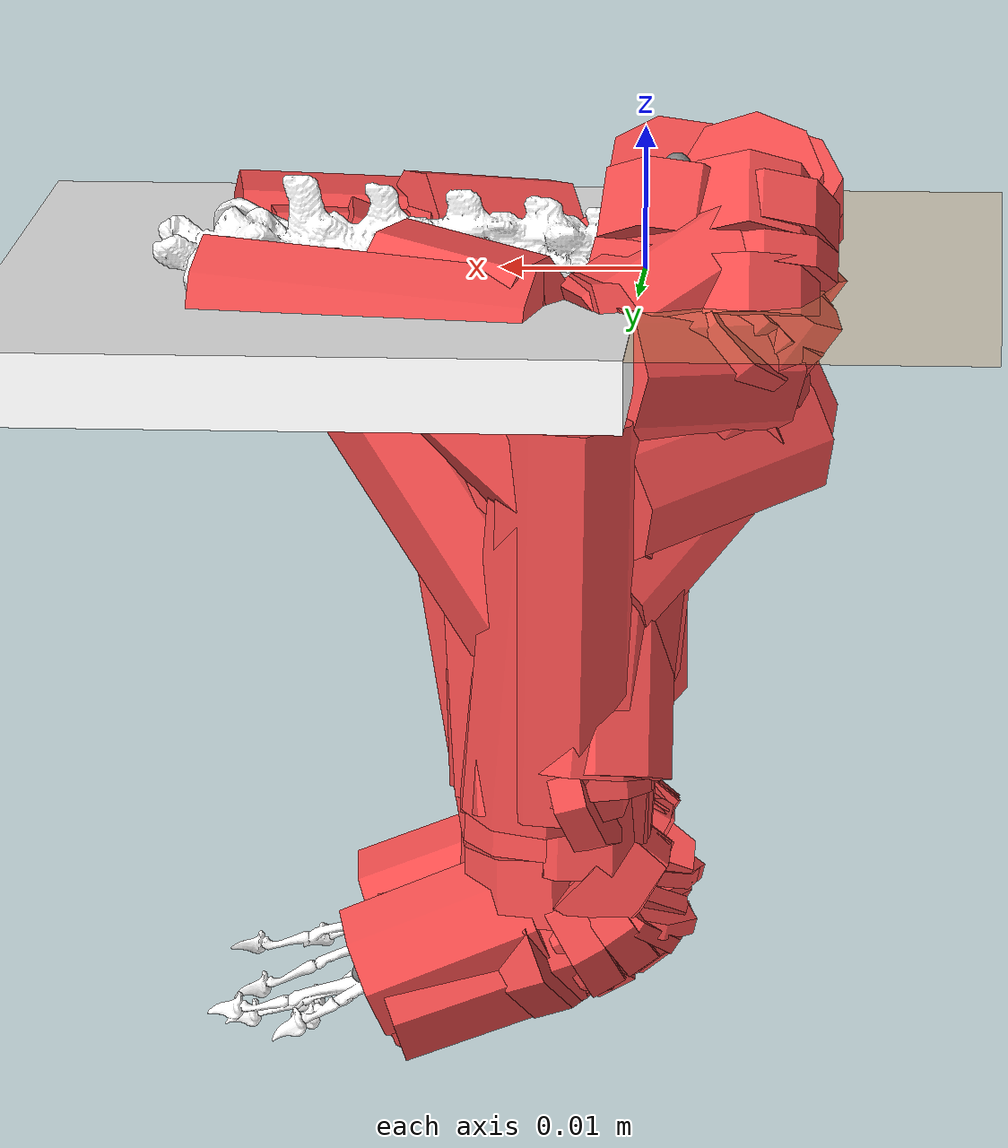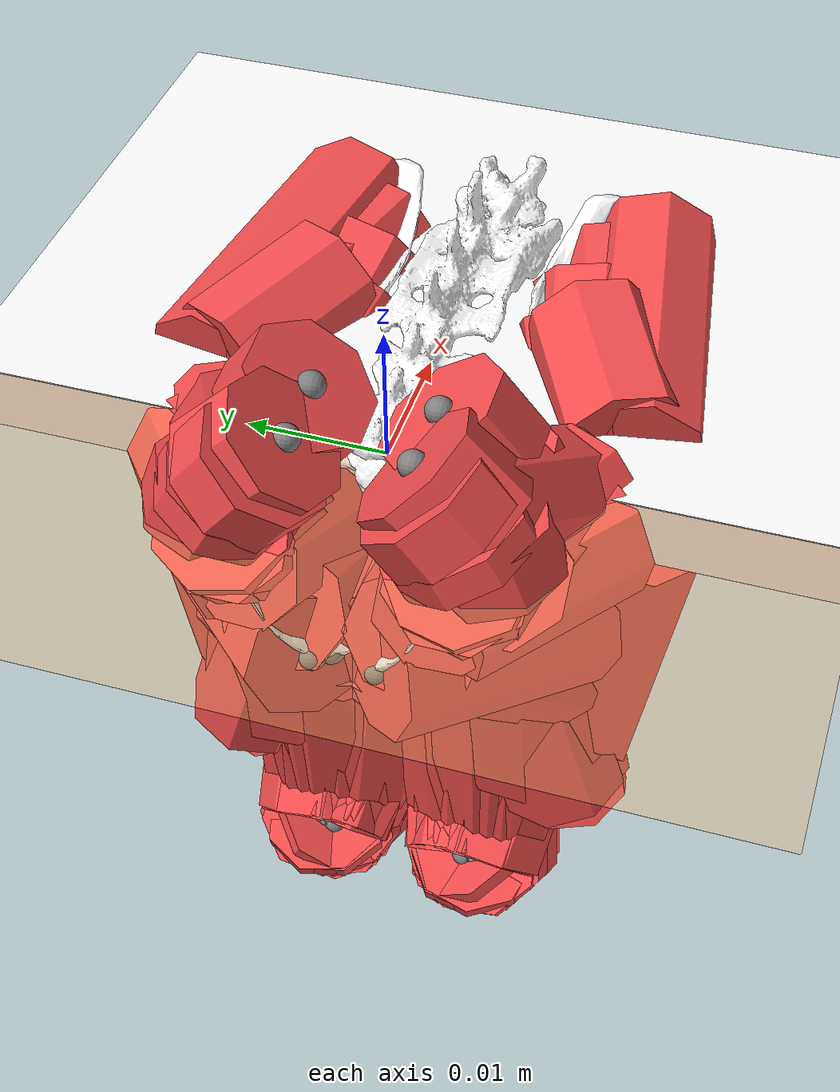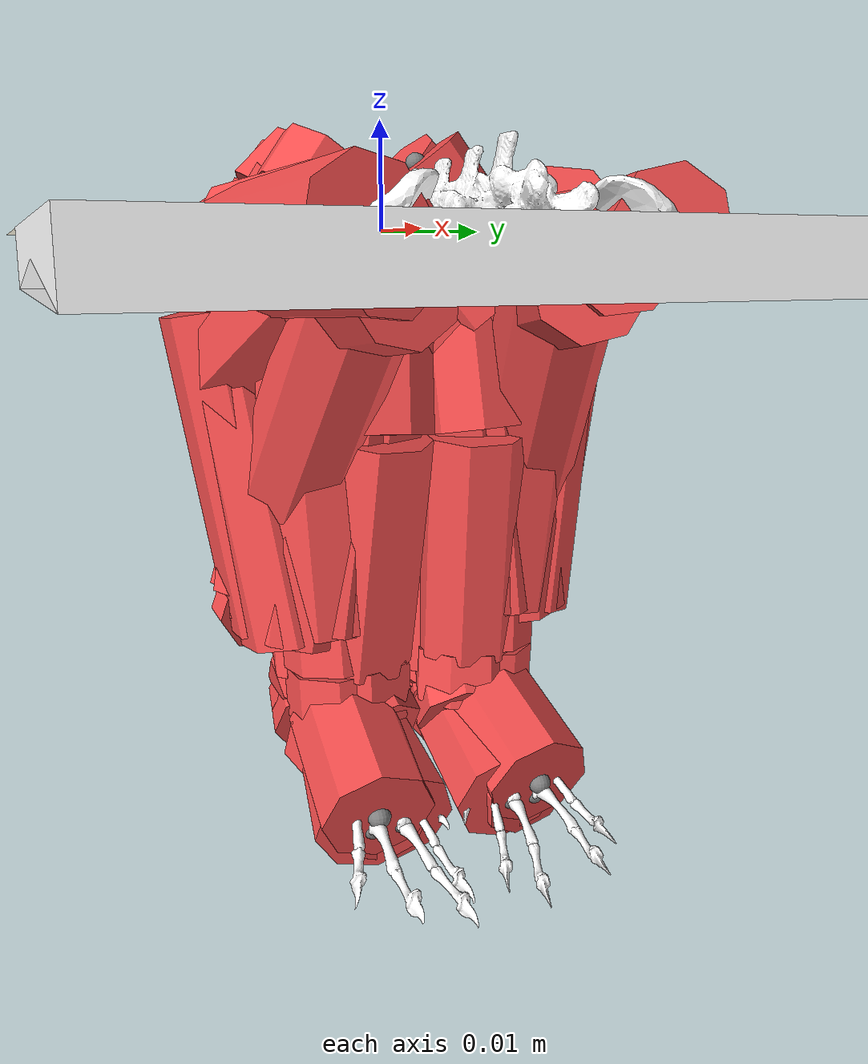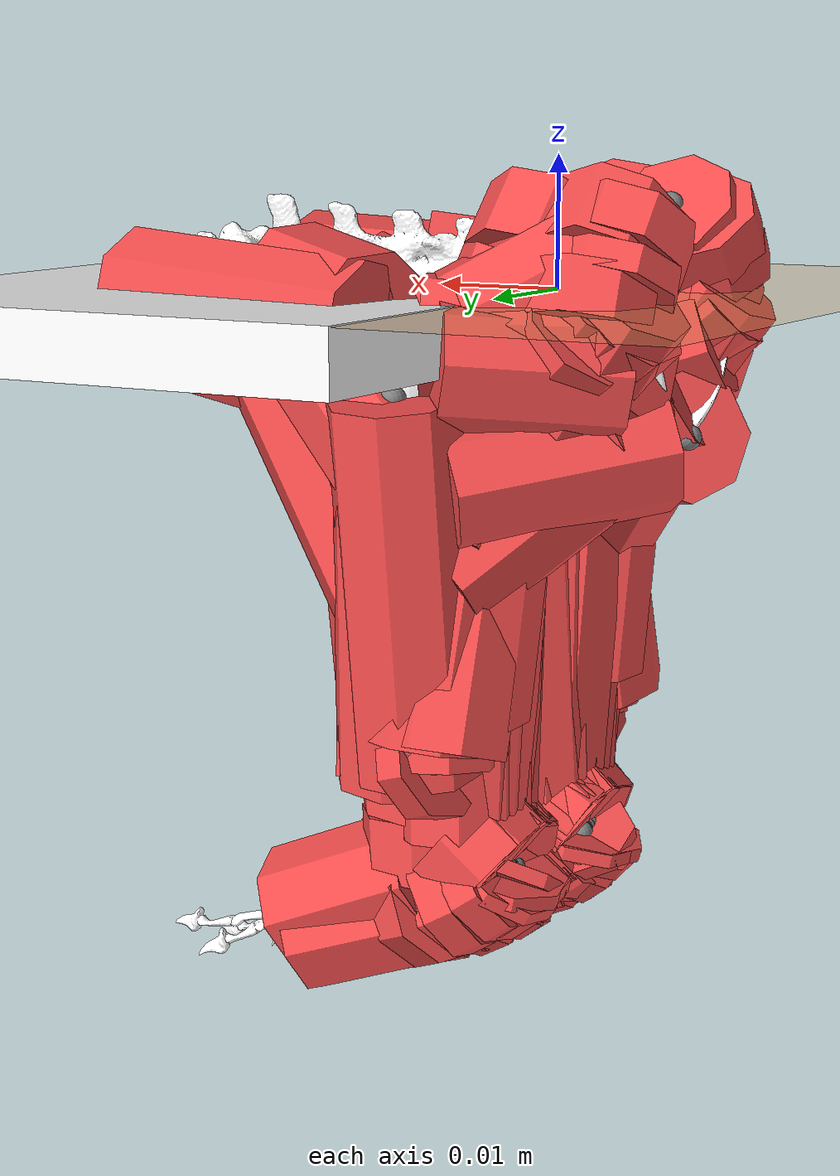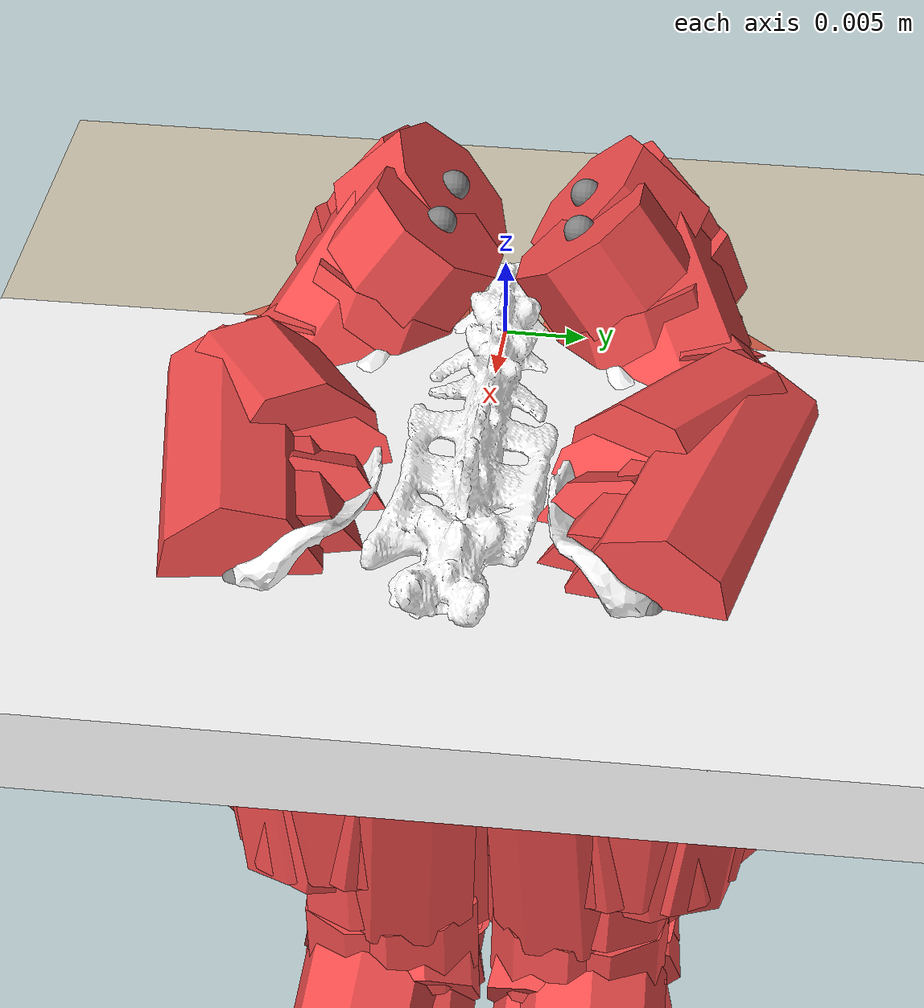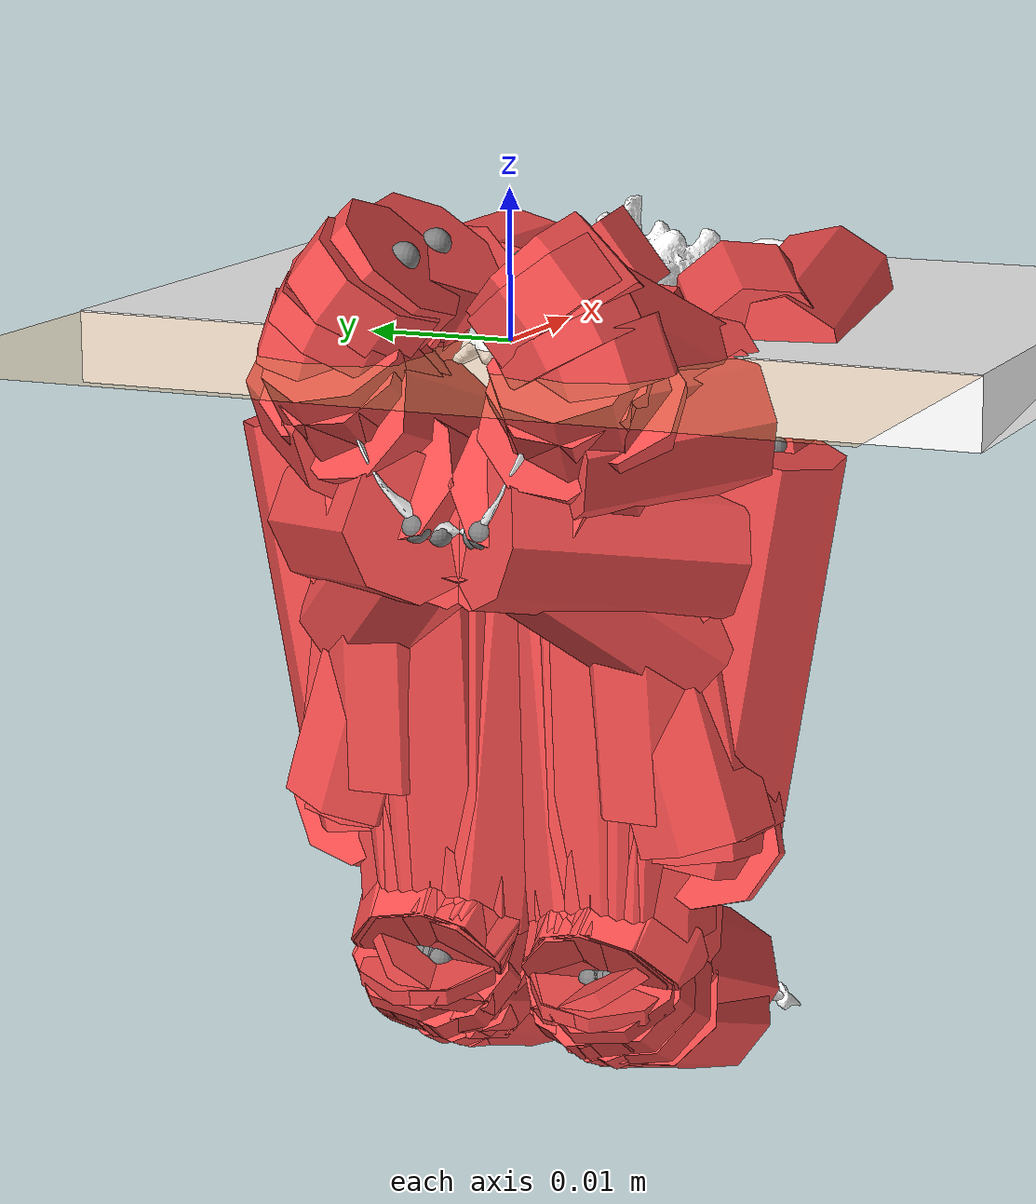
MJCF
<mujoco model="template">
  <!-- This model has been converted from an OpenSim model. Model conversion by MyoConverter https://github.com/MyoHub/myoconverter. This model is licensed under Apache 2.0. -->
  <!-- Credits from the original OpenSim model. Note! If the following has any license information, it applies to the original OpenSim model. Credits: Model authors names.. -->
  <!-- Note: inertiagrouprange="0 1" means that groups 0-1 will be used to infer masses/inertias, and groups 2-5 are
  only for visualisation (e.g. wrapping objects) !-->
  <compiler inertiafromgeom="auto" angle="radian" balanceinertia="true" boundmass="0.001" boundinertia="0.001" inertiagrouprange="0 1">
    <lengthrange inttotal="50" useexisting="true"/>
  </compiler>
  <option collision="predefined"/>
  <visual>
    <scale framelength="0.5" framewidth="0.01"/>
  </visual>
  <default>
    <joint limited="true" damping="0.05" armature="0.00001" stiffness="0"/>
    <geom rgba="0.8 0.6 .4 1" margin="0.001"/>
    <site size="0.001"/>
    <tendon width="0.005" rgba=".95 .3 .3 1" limited="false"/>
    <default class="muscle">
      <muscle ctrllimited="true" ctrlrange="0 1" scale="200"/>
    </default>
    <default class="motor">
      <general gainprm="5 0 0 0 0 0 0 0 0 0"/>
    </default>
  </default>
  <option timestep="0.002"/>
  <!-- nuser_jnt=1, the parameter is used to store default value of the joint, and nkey=1 to store keyframe with
   default joint positions set !-->
  <size njmax="1000" nconmax="400" nuser_jnt="1" nkey="1"/>
  <worldbody>
    <!-- The converter script assumes a body named 'ground' exists as a child element of worldbody -->
    <body name="ground" euler="1.571 0 0">
      <geom name="ground-plane" pos="0 0 0" euler="-1.571 0 0" size="10 10 0.125" type="plane" rgba="1.0 0.7 0.4 1.0" condim="3"/>
      <geom name="ground_geom_1" type="mesh" pos="0 0 0" euler="0 0 0" mesh="ground_geom_1_ground" rgba="1 1 1 1" group="0"/>
    </body>
    <light directional="true"/>
    <body name="spine" pos="0 0 0" euler="1.571 0 0">
      <inertial mass="0.12" pos="0 0 0" fullinertia="4.7999999999999998e-06 4.7999999999999998e-06 4.7999999999999998e-06 0 0 0"/>
      <geom name="spine_geom_1" type="mesh" mesh="spine_geom_1_spine" rgba="1 1 1 1" group="0"/>
      <joint name="sacrum_x" range="-0.1 0.25" limited="true" user="0.0" ref="0" axis="1 0 0" type="slide" damping="0" stiffness="0"/>
      <joint name="sacrum_y" range="0 0.2" limited="true" user="0.05" ref="0" axis="0 1 0" type="slide" damping="0" stiffness="0"/>
      <joint name="sacrum_z" range="-0.1 0.1" limited="true" user="0.0" ref="0" axis="0 0 1" type="slide" damping="0" stiffness="0"/>
      <joint name="sacrum_pitch" range="-1.571 1.571" limited="true" user="0.52359878" ref="0" axis="0 0 1" type="hinge" damping="0" stiffness="0"/>
      <joint name="sacrum_roll" range="-1.571 1.571" limited="true" user="0.0" ref="0" axis="1 0 0" type="hinge" damping="0" stiffness="0"/>
      <joint name="sacrum_yaw" range="-1.571 1.571" limited="true" user="0.0" ref="0" axis="0 1 0" type="hinge" damping="0" stiffness="0"/>
      <body name="pelvis_r" pos="0.005 -0.003 0.01" euler="-0 0 0">
        <inertial mass="0.02" pos="0 0 0" fullinertia="3.9999999999999998e-06 3.4999999999999999e-06 3.4999999999999999e-06 0 0 0"/>
        <geom name="pelvis_r_geom_1" type="mesh" mesh="pelvis_r_geom_1_pelvis_r" rgba="1 1 1 1" group="0"/>
        <joint name="sacroiliac_r_flx" range="-0.02301 0.1515" limited="true" user="0.06457718" ref="0" axis="0 0 1" type="hinge"/>
        <body name="femur_r" pos="0 0 0" euler="-0 0 0">
          <inertial mass="0.02" pos="0 -0.014999999999999999 0" fullinertia="1.6199999999999999e-06 2.4999999999999999e-07 1.6199999999999999e-06 0 0 0"/>
          <geom name="femur_r_geom_1" type="mesh" mesh="femur_r_geom_1_femur_r" rgba="1 1 1 1" group="0"/>
          <joint name="hip_r_flx" range="-0.8727 1.222" limited="true" user="0.6981317" ref="0" axis="0 0 1" type="hinge"/>
          <joint name="hip_r_add" range="-0.8727 0.3491" limited="true" user="-0.17453293" ref="0" axis="1 0 0" type="hinge"/>
          <joint name="hip_r_int" range="-0.8727 0.6981" limited="true" user="0.0" ref="0" axis="0 1 0" type="hinge"/>
          <body name="tibia_r" pos="0.00057 -0.03996 -0.003816" euler="-0 0 0">
            <inertial mass="0.02" pos="0 0.014999999999999999 0" fullinertia="1.6199999999999999e-06 2.4999999999999999e-07 1.6199999999999999e-06 0 0 0"/>
            <geom name="tibia_r_geom_1" type="mesh" mesh="tibia_r_geom_1_tibia_r" rgba="1 1 1 1" group="0"/>
            <joint name="knee_r_translation1" range="-0.005239 -0.001413" limited="true" user="-0.0034729536543709628" ref="0" axis="1 0 0" type="slide"/>
            <joint name="knee_r_translation2" range="-0.03425 -0.03206" limited="true" user="-0.03396322535266436" ref="0" axis="0 1 0" type="slide"/>
            <joint name="knee_r_translation3" range="0.002381 0.002904" limited="true" user="0.0029010542275394995" ref="0" axis="0 0 1" type="slide"/>
            <joint name="knee_r_flx" range="-2.618 -0.3491" limited="true" user="-2.0943951" ref="0" axis="0 0 1" type="hinge"/>
            <joint name="knee_r_rotation2" range="-0.08727 0.06458" limited="true" user="-0.05238438333586499" ref="0" axis="1 0 0" type="hinge"/>
            <joint name="knee_r_rotation3" range="-2.618 -0.3491" limited="false" user="-2.0943951" ref="0" axis="0 1 0" type="hinge"/>
            <body name="foot_r" pos="0 0 0" euler="-0 0 0">
              <inertial mass="0.02" pos="0.0070000000000000001 -0.0050000000000000001 0" fullinertia="2.4999999999999999e-07 1.6199999999999999e-06 1.6199999999999999e-06 0 0 0"/>
              <geom name="foot_r_geom_1" type="mesh" mesh="foot_r_geom_1_foot_r" rgba="1 1 1 1" group="0"/>
              <joint name="ankle_r_translation1" range="-1e-06 0" limited="true" user="0.0" ref="0" axis="1 0 0" type="slide"/>
              <joint name="ankle_r_translation2" range="-1e-06 0" limited="true" user="0.0" ref="0" axis="0 1 0" type="slide"/>
              <joint name="ankle_r_translation3" range="-1e-06 0" limited="true" user="0.0" ref="0" axis="0 0 1" type="slide"/>
              <joint name="ankle_r_flx" range="-0.5236 1.047" limited="true" user="0.87266463" ref="0" axis="0 0 1" type="hinge"/>
              <joint name="ankle_r_add" range="-0.08727 0.6109" limited="true" user="-0.08726646" ref="0" axis="1 0 0" type="hinge"/>
              <joint name="ankle_r_int" range="-0.8727 0.2618" limited="true" user="0.0" ref="0" axis="0 1 0" type="hinge"/>
              <site name="R_MG_R_MG_foot_r_via_4" pos="-0.0043644856609585843 -0.00041501861665327647 -0.00061089867844681925"/>
              <site name="R_MG_R_MG_foot_r_insertion_5" pos="-0.0042570957722349242 -0.0014280992062151757 -8.0326946730908651e-05"/>
              <site name="R_LG_R_LG_foot_r_via_4" pos="-0.004894253784045623 -0.00028943550213634259 0.00078615805026828109"/>
              <site name="R_LG_R_LG_foot_r_insertion_5" pos="-0.0042357562328421451 -0.0012702836426840927 0.00088693901215988855"/>
              <site name="R_Pla_R_Pla_foot_r_via_4" pos="-0.004887494269850412 -0.00034410885663031787 0.00038947277861585048"/>
              <site name="R_Pla_R_Pla_foot_r_insertion_5" pos="-0.0046019319914399328 -0.0014604795692403825 0.00037014349640615302"/>
              <site name="R_Sol_R_Sol_foot_r_via_3" pos="-0.0048551230466509446 -0.00039237013978514614 7.707982709098416e-05"/>
              <site name="R_Sol_R_Sol_foot_r_insertion_4" pos="-0.0045851940040285248 -0.0014738786473782223 4.8463799423735434e-05"/>
              <site name="R_TA_R_TA_foot_r_via_4" pos="0.001996197758142419 -0.0011377690019365959 -0.00081153929806410748"/>
              <site name="R_TA_R_TA_foot_r_insertion_5" pos="0.0042023791961630424 -0.0029182895655272007 -0.0012557349732445311"/>
              <site name="R_EDL_R_EDL_foot_r_via_4" pos="0.0015741230047112737 -0.0010897785031953443 0.00086941752043996992"/>
              <site name="R_EDL_R_EDL_foot_r_insertion_5" pos="0.013390391070901718 -0.0058553279543593828 0.0015071685394595219"/>
              <site name="R_TP_R_TP_foot_r_via_3" pos="-0.0050140896766588741 -0.00048412806427301531 -0.00049705131055248182"/>
              <site name="R_TP_R_TP_foot_r_via_4" pos="-0.0028008946089127509 -0.002098685722790494 -0.00025052440195132825"/>
              <site name="R_TP_R_TP_foot_r_insertion_5" pos="0.0013018182657607408 -0.0033217581945711562 -0.0012558791160364674"/>
              <site name="R_FDL_R_FDL_foot_r_via_3" pos="-0.0049006103147679917 -0.00042815984010432921 -0.00027834619676577539"/>
              <site name="R_FDL_R_FDL_foot_r_via_4" pos="-0.0030193504886048034 -0.0018117857770755595 -4.9271997420705446e-05"/>
              <site name="R_FDL_R_FDL_foot_r_via_5" pos="-0.00046647713525273336 -0.0032449911643460537 -0.00027529150576495833"/>
              <site name="R_FDL_R_FDL_foot_r_insertion_6" pos="0.012088475753531509 -0.0074525944861724928 0.0016798500791248641"/>
              <site name="R_FHL_R_FHL_foot_r_via_3" pos="-0.0046550214287895599 -0.00058999812693798313 -0.00060064011032940918"/>
              <site name="R_FHL_R_FHL_foot_r_via_4" pos="-0.0027668817167818549 -0.0020698947552325654 -0.00067195012401080655"/>
              <site name="R_FHL_R_FHL_foot_r_via_5" pos="0.00020941022541089106 -0.0033863339029106087 -0.00047099016711681563"/>
              <site name="R_FHL_R_FHL_foot_r_insertion_6" pos="0.012160947946933209 -0.0074054899112189296 -0.00092222726417313418"/>
              <site name="R_Per_R_Per_foot_r_via_3" pos="-0.0045230898912524652 -0.00031568079336937615 0.0011571079090557197"/>
              <site name="R_Per_R_Per_foot_r_via_4" pos="-0.002479890409816176 -0.0017431001101783027 0.0014339768017218699"/>
              <site name="R_Per_R_Per_foot_r_via_5" pos="-0.00027051557237839797 -0.0029929302324747773 0.0017608400357515424"/>
              <site name="R_Per_R_Per_foot_r_insertion_6" pos="0.0024289298116546253 -0.004097917385018154 0.00072771846111249544"/>
              <site name="RTOE_marker" group="4" pos="0.015 -0.005 0.005" rgba="1 0.1 0.5 0.5" size="0.01"/>
            </body>
            <site name="R_BFa_R_BFa_tibia_r_insertion_4" pos="-0.0029720501322021992 0.032503141785738821 0.0013564570622283541"/>
            <site name="R_BFp_R_BFp_tibia_r_via_2" pos="-0.0033477343146640932 0.027050959773747919 0.00058516519106733677"/>
            <site name="R_BFp_R_BFp_tibia_r_insertion_3" pos="0.0020778283816709551 0.027409867780973429 0.00013043053046951162"/>
            <site name="R_STp_R_STp_tibia_r_insertion_2" pos="0.0020082787983591627 0.027605769953851642 -0.002090324526858478"/>
            <site name="R_STa_R_STa_tibia_r_insertion_4" pos="0.0020082787983591627 0.027605769953851642 -0.002090324526858478"/>
            <site name="R_SM_R_SM_tibia_r_insertion_2" pos="0.00053037040221139793 0.034227060991345711 -0.0026972547044311714"/>
            <site name="R_GP_R_GP_tibia_r_insertion_2" pos="0.0019982421256348722 0.028432489897799618 -0.0028146832904258887"/>
            <site name="R_GA_R_GA_tibia_r_insertion_2" pos="0.0015522927682110176 0.03082793164133741 -0.0028166017014169195"/>
            <site name="R_AM_R_AM_tibia_r_insertion_2" pos="0.00090309811687147449 0.0324771009575541 -0.002738506958637131"/>
            <site name="R_RF_R_RF_tibia_r_via_3" pos="0.0037061437979996068 0.03985708456847227 -0.0016156324939123404"/>
            <site name="R_VL_R_VL_tibia_r_via_3" pos="0.0029962673848681867 0.040226642049806569 0.00088801516381843324"/>
            <site name="R_VL_R_VL_tibia_r_insertion_4" pos="0.0049526311116486667 0.035595398095711946 -0.00040792364024868353"/>
            <site name="R_VI_R_VI_tibia_r_via_3" pos="0.0032547248156170826 0.039915792668088527 -0.00037621271137921097"/>
            <site name="R_VI_R_VI_tibia_r_insertion_4" pos="0.0049526311116486667 0.035595398095711946 -0.00040792364024868353"/>
            <site name="R_VM_R_VM_tibia_r_via_3" pos="0.0038690938261241935 0.039709119885925195 -0.0035536532806488066"/>
            <site name="R_VM_R_VM_tibia_r_insertion_4" pos="0.0049526311116486667 0.035595398095711946 -0.00040792364024868353"/>
            <site name="R_MG_R_MG_tibia_r_via_2" pos="-0.00061028462782205725 0.034471160109716133 -0.0045379327982593021"/>
            <site name="R_MG_R_MG_tibia_r_via_3" pos="-0.0010129592533992485 0.0018070744624021501 -0.0015238944507650117"/>
            <site name="R_LG_R_LG_tibia_r_via_2" pos="-0.0034114162817267214 0.035187681314255231 0.0027594054352239007"/>
            <site name="R_LG_R_LG_tibia_r_via_3" pos="-0.0013326354885805211 0.0025494762848000674 0.0012973353810557706"/>
            <site name="R_Pla_R_Pla_tibia_r_via_2" pos="-0.0035939908554636036 0.034382702995623016 0.0020539644389975941"/>
            <site name="R_Pla_R_Pla_tibia_r_via_3" pos="-0.0013122201994958472 0.0025409109059577467 0.00089537310342807045"/>
            <site name="R_Sol_R_Sol_tibia_r_origin_1" pos="-0.0037946950964456707 0.034427222488087113 0.00036983979369532632"/>
            <site name="R_Sol_R_Sol_tibia_r_via_2" pos="-0.0012815748314852276 0.0025280534251900383 0.00029198797019791838"/>
            <site name="R_TA_R_TA_tibia_r_origin_1" pos="0.003815335894026634 0.035039932453186422 -0.0020320176860204563"/>
            <site name="R_TA_R_TA_tibia_r_via_2" pos="0.0054419715356187354 0.025474704095827624 -0.0015789884196202835"/>
            <site name="R_TA_R_TA_tibia_r_via_3" pos="0.0018650135746135308 0.0040108442228638727 -0.0006927550308904319"/>
            <site name="R_EDL_R_EDL_tibia_r_via_2" pos="-0.00033362622880194078 0.037562099985690073 0.0026941073247637825"/>
            <site name="R_EDL_R_EDL_tibia_r_via_3" pos="0.0016358583241553332 0.0038631519865891598 0.0011179446882720939"/>
            <site name="R_TP_R_TP_tibia_r_origin_1" pos="-0.0018797778041290724 0.032605700298817597 -0.0014887303119028061"/>
            <site name="R_TP_R_TP_tibia_r_via_2" pos="-0.0011105028653790195 0.0019598594204923853 -0.00090916644804106322"/>
            <site name="R_FDL_R_FDL_tibia_r_origin_1" pos="-0.0021417321809504108 0.034400201870842771 -0.00089606904811544087"/>
            <site name="R_FDL_R_FDL_tibia_r_via_2" pos="-0.00098622504099876284 0.0024109460510779515 -0.00054118507680070817"/>
            <site name="R_FHL_R_FHL_tibia_r_origin_1" pos="-0.00068479086563551239 0.032342564889487738 -0.0014224309108078121"/>
            <site name="R_FHL_R_FHL_tibia_r_via_2" pos="-0.0010899130792478137 0.0022516265945384736 -0.0012670111501499604"/>
            <site name="R_Per_R_Per_tibia_r_origin_1" pos="-0.0022409419138834574 0.035602813132340254 0.002786967776420421"/>
            <site name="R_Per_R_Per_tibia_r_via_2" pos="-0.0013511214206747757 0.0025572321882792737 0.0016613100148637099"/>
            <site name="R_Pop_R_Pop_tibia_r_via_3" pos="-0.0032422228515295404 0.034934618194919428 -0.00047687342838239146"/>
            <site name="R_Pop_R_Pop_tibia_r_insertion_4" pos="0.0018743036176071073 0.025692425237281401 -0.0021999081037133725"/>
            <site name="RANK_marker" group="4" pos="0 0 0.004" rgba="1 0.1 0.5 0.5" size="0.01"/>
          </body>
          <site name="R_CF_R_CF_femur_r_insertion_4" pos="-0.0023353198257833985 -0.027830132062425697 -0.00033572032974357909"/>
          <site name="R_QF_R_QF_femur_r_insertion_2" pos="-0.0028598295892632007 -0.0012439485697935946 0.0051866869305703753"/>
          <site name="R_TFL_R_TFL_femur_r_insertion_2" pos="0.001342896241844706 -0.020348407796310475 0.0016722824707312281"/>
          <site name="R_GMa_R_GMa_femur_r_insertion_2" pos="-0.00066399672874976271 -0.0085773703672146762 0.0057564426420532505"/>
          <site name="R_GMe_R_GMe_femur_r_insertion_2" pos="0.0016910651379157481 0.0010714069762145543 0.0057686028708801547"/>
          <site name="R_GMi_R_GMi_femur_r_insertion_2" pos="0.0016981290501464634 4.4895841904476997e-05 0.0050684331618505093"/>
          <site name="R_Pir_R_Pir_femur_r_insertion_2" pos="0.0020734803408357485 0.0017136988029230961 0.0050413676348091824"/>
          <site name="R_AL_R_AL_femur_r_insertion_2" pos="-0.0020027319269709681 -0.015179618048449091 0.0016696879973486572"/>
          <site name="R_AB_R_AB_femur_r_insertion_2" pos="-0.0019248092692481515 -0.017192679034441626 0.0021014018629129218"/>
          <site name="R_Pec_R_Pec_femur_r_insertion_2" pos="-0.0028720102484357567 -0.010311417724799271 0.0038135519618526185"/>
          <site name="R_IP_R_IP_femur_r_insertion_2" pos="-0.00059747480435698918 -0.0040958672151299638 0.0013580898171673436"/>
          <site name="R_OE_R_OE_femur_r_insertion_2" pos="-0.0023364452903325023 -0.0012154325220975833 0.0017567722384606436"/>
          <site name="R_OI_R_OI_femur_r_via_2" pos="-0.0010715087481183924 0.00017202783444896256 0.0031542958124144978"/>
          <site name="R_GS_R_GS_femur_r_insertion_2" pos="-0.00016744212779093196 -0.0060346518923546791 0.0020777992433516166"/>
          <site name="R_GI_R_GI_femur_r_insertion_2" pos="-0.002167839897819439 -9.4652808305946455e-05 0.0020078099502321678"/>
          <site name="R_RF_R_RF_femur_r_via_2" pos="0.0030353602357688831 -0.031714793208158731 -0.0014652308022125478"/>
          <site name="R_VL_R_VL_femur_r_origin_1" pos="-0.0005698329738700439 -0.003642219697407737 0.006674742915072621"/>
          <site name="R_VL_R_VL_femur_r_via_2" pos="0.00012852511579401727 -0.031938231301560836 0.0019768686699122382"/>
          <site name="R_VI_R_VI_femur_r_origin_1" pos="7.1254133784281754e-05 -0.010078513779473046 0.0048028747178181785"/>
          <site name="R_VI_R_VI_femur_r_via_2" pos="0.0020977933465365375 -0.032845730889325325 0.0012127442992602381"/>
          <site name="R_VM_R_VM_femur_r_origin_1" pos="-0.0005446529026655318 -0.0050106716264102791 0.0014707079771160481"/>
          <site name="R_VM_R_VM_femur_r_via_2" pos="0.0018615359313195004 -0.031741287411034623 -0.0034865551248776478"/>
          <site name="R_MG_R_MG_femur_r_origin_1" pos="-0.00035650363420243686 -0.030232694694559165 -0.0043723770116074739"/>
          <site name="R_LG_R_LG_femur_r_origin_1" pos="-0.00083072830972111299 -0.02965906786469592 0.0030686954131009768"/>
          <site name="R_Pla_R_Pla_femur_r_origin_1" pos="-0.00094769441900232688 -0.028815973185495475 0.0024526954438854887"/>
          <site name="R_EDL_R_EDL_femur_r_origin_1" pos="-0.0011576457748776288 -0.031367727648900792 0.0023369055312103433"/>
          <site name="R_Pop_R_Pop_femur_r_origin_1" pos="-0.00033475630240283386 -0.030685985823212858 0.0027704835868093049"/>
          <site name="R_Pop_R_Pop_femur_r_via_2" pos="-0.0025438011937069069 -0.030008040292098304 0.0031410459524080572"/>
          <site name="RKNE_marker" group="4" pos="0 -0.035 0.003" rgba="1 0.1 0.5 0.5" size="0.01"/>
        </body>
        <site name="R_BFa_R_BFa_pelvis_r_origin_1" pos="-0.012174862244325017 0.0092464330153996591 -0.0057814427651885752"/>
        <site name="R_BFa_R_BFa_pelvis_r_via_2" pos="-0.012288525099114279 0.0050841758719611559 -0.0015115191620048733"/>
        <site name="R_BFa_R_BFa_pelvis_r_via_3" pos="-0.012335447948644586 0.0012850001404715603 -0.00012088885675958991"/>
        <site name="R_BFp_R_BFp_pelvis_r_origin_1" pos="-0.014898166633248432 0.0035808503985728939 -0.0019908711637354574"/>
        <site name="R_CF_R_CF_pelvis_r_origin_1" pos="-0.0070073138976448814 0.0094484925828902822 -0.0056452009629855814"/>
        <site name="R_CF_R_CF_pelvis_r_via_2" pos="-0.0064792200759978928 0.0052038469787676379 -0.0025571593066870506"/>
        <site name="R_CF_R_CF_pelvis_r_via_3" pos="-0.0054509173994872805 0.0011654291010667209 -0.0010876266300662765"/>
        <site name="R_STp_R_STp_pelvis_r_origin_1" pos="-0.014684335749941855 0.0026020037634386845 -0.0020882888878995427"/>
        <site name="R_STa_R_STa_pelvis_r_origin_1" pos="-0.013508603852453577 0.0085812897016205782 -0.004937057563502086"/>
        <site name="R_STa_R_STa_pelvis_r_via_2" pos="-0.013487316912130712 0.0056994324568380508 -0.0025945877661864005"/>
        <site name="R_STa_R_STa_pelvis_r_via_3" pos="-0.013497670087086865 0.0037587538333285373 -0.001524656219424176"/>
        <site name="R_SM_R_SM_pelvis_r_origin_1" pos="-0.014723497528866375 -0.00023384221531321512 -0.0027977927923190822"/>
        <site name="R_QF_R_QF_pelvis_r_origin_1" pos="-0.013255161759989181 -0.0024002808514835983 -0.0035466034569641165"/>
        <site name="R_TFL_R_TFL_pelvis_r_origin_1" pos="0.015452523160770604 0.00072907793733371484 -0.0017377071679405658"/>
        <site name="R_GMa_R_GMa_pelvis_r_origin_1" pos="0.013526315272142169 0.0025045975270483346 -0.0012825828368993337"/>
        <site name="R_GMe_R_GMe_pelvis_r_origin_1" pos="0.024571187130225835 0.0025272676130997686 0.0017832149694025877"/>
        <site name="R_GMi_R_GMi_pelvis_r_origin_1" pos="0.022163495409719375 0.0010493918239506766 -0.00083416444962816291"/>
        <site name="R_Pir_R_Pir_pelvis_r_origin_1" pos="0.012118913238697682 0.0032360582478523749 -0.00025666934847505714"/>
        <site name="R_GP_R_GP_pelvis_r_origin_1" pos="-0.013968234170482263 -0.0044135174362874762 -0.0052347506630223591"/>
        <site name="R_GA_R_GA_pelvis_r_origin_1" pos="-0.013444368394770947 -0.0082503918942580558 -0.0085815363608384172"/>
        <site name="R_AL_R_AL_pelvis_r_origin_1" pos="-0.0045917524811206747 -0.0054291070821665425 -0.0058440757056997623"/>
        <site name="R_AM_R_AM_pelvis_r_origin_1" pos="-0.012185387389508397 -0.0082968921810472693 -0.0085981312841527206"/>
        <site name="R_AB_R_AB_pelvis_r_origin_1" pos="-0.011608173774338457 -0.0072948744524240468 -0.0079299151837134256"/>
        <site name="R_Pec_R_Pec_pelvis_r_origin_1" pos="-0.014821106185708824 -0.0077184528843072973 -0.0076826326335045709"/>
        <site name="R_IP_R_IP_pelvis_r_origin_1" pos="0.020315964394375118 -0.0011906066726147459 -0.0024228790968182602"/>
        <site name="R_OE_R_OE_pelvis_r_origin_1" pos="-0.0090266909374477535 -0.0015364560118290658 -0.003252042798742103"/>
        <site name="R_OI_R_OI_pelvis_r_origin_1" pos="-0.012714713608858078 -0.00011935301194733916 -0.0021865783049474317"/>
        <site name="R_GS_R_GS_pelvis_r_origin_1" pos="0.017845615047809113 0.0015477716354723751 -0.0013502313756603487"/>
        <site name="R_GI_R_GI_pelvis_r_origin_1" pos="-0.011410216957107179 0.0054292776452135247 -0.0027069621690553524"/>
        <site name="R_RF_R_RF_pelvis_r_origin_1" pos="0.0045996236847650057 -0.00045864417595834709 0.0010492012082629412"/>
        <site name="RASI_marker" group="4" pos="0.028 0.004 0.003" rgba="1 0.1 0.5 0.5" size="0.01"/>
        <site name="RHIP_marker" group="4" pos="-0.001 0.001 0.01" rgba="1 0.1 0.5 0.5" size="0.01"/>
      </body>
      <body name="pelvis_l" pos="0.005 -0.003 -0.01" euler="-0 0 0">
        <inertial mass="0.02" pos="0 0 -0" fullinertia="3.9999999999999998e-06 3.4999999999999999e-06 3.4999999999999999e-06 0 -0 -0"/>
        <geom name="pelvis_l_geom_1" type="mesh" mesh="pelvis_l_geom_1_pelvis_r" rgba="1 1 1 1" group="0"/>
        <joint name="sacroiliac_l_flx" range="-0.02301 0.1515" limited="true" user="0.06457718" ref="0" axis="0 0 1" type="hinge"/>
        <body name="femur_l" pos="0 0 0" euler="-0 0 0">
          <inertial mass="0.02" pos="0 -0.014999999999999999 -0" fullinertia="1.6199999999999999e-06 2.4999999999999999e-07 1.6199999999999999e-06 0 -0 -0"/>
          <geom name="femur_l_geom_1" type="mesh" mesh="femur_l_geom_1_femur_r" rgba="1 1 1 1" group="0"/>
          <joint name="hip_l_flx" range="-0.8727 1.222" limited="true" user="0.6981317" ref="0" axis="0 0 1" type="hinge"/>
          <joint name="hip_l_add" range="-0.8727 0.3491" limited="true" user="0.17453293" ref="0" axis="-1 -0 -0" type="hinge"/>
          <joint name="hip_l_int" range="-0.8727 0.6981" limited="true" user="-0.0" ref="0" axis="-0 -1 -0" type="hinge"/>
          <body name="tibia_l" pos="0.00057 -0.03996 0.003816" euler="-0 0 0">
            <inertial mass="0.02" pos="0 0.014999999999999999 -0" fullinertia="1.6199999999999999e-06 2.4999999999999999e-07 1.6199999999999999e-06 0 -0 -0"/>
            <geom name="tibia_l_geom_1" type="mesh" mesh="tibia_l_geom_1_tibia_r" rgba="1 1 1 1" group="0"/>
            <joint name="knee_l_translation1" range="-0.005239 -0.001413" limited="true" user="-0.0034729536543709628" ref="0" axis="1 0 0" type="slide"/>
            <joint name="knee_l_translation2" range="-0.03425 -0.03206" limited="true" user="-0.03396322535266436" ref="0" axis="0 1 0" type="slide"/>
            <joint name="knee_l_translation3" range="-0.002904 -0.002381" limited="true" user="-0.0029010542275394995" ref="0" axis="0 0 1" type="slide"/>
            <joint name="knee_l_flx" range="-2.618 -0.3491" limited="true" user="-2.0943951" ref="0" axis="0 0 1" type="hinge"/>
            <joint name="knee_l_rotation2" range="-0.06458 0.08727" limited="true" user="0.05238438333586499" ref="0" axis="1 0 0" type="hinge"/>
            <joint name="knee_l_rotation3" range="-2.618 -0.3491" limited="false" user="-2.0943951" ref="0" axis="0 1 0" type="hinge"/>
            <body name="foot_l" pos="0 0 0" euler="-0 0 0">
              <inertial mass="0.02" pos="0.0070000000000000001 -0.0050000000000000001 -0" fullinertia="2.4999999999999999e-07 1.6199999999999999e-06 1.6199999999999999e-06 0 -0 -0"/>
              <geom name="foot_l_geom_1" type="mesh" mesh="foot_l_geom_1_foot_r" rgba="1 1 1 1" group="0"/>
              <joint name="ankle_l_translation1" range="-1e-06 0" limited="true" user="0.0" ref="0" axis="1 0 0" type="slide"/>
              <joint name="ankle_l_translation2" range="-1e-06 0" limited="true" user="0.0" ref="0" axis="0 1 0" type="slide"/>
              <joint name="ankle_l_translation3" range="-1e-06 -0" limited="true" user="0.0" ref="0" axis="0 0 1" type="slide"/>
              <joint name="ankle_l_flx" range="-0.5236 1.047" limited="true" user="0.87266463" ref="0" axis="0 0 1" type="hinge"/>
              <joint name="ankle_l_add" range="-0.08727 0.6109" limited="true" user="0.08726646" ref="0" axis="-1 -0 -0" type="hinge"/>
              <joint name="ankle_l_int" range="-0.8727 0.2618" limited="true" user="-0.0" ref="0" axis="-0 -1 -0" type="hinge"/>
              <site name="L_MG_L_MG_foot_l_via_4" pos="-0.0043644856609585843 -0.00041501861665327647 0.00061089867844681925"/>
              <site name="L_MG_L_MG_foot_l_insertion_5" pos="-0.0042570957722349242 -0.0014280992062151757 8.0326946730908651e-05"/>
              <site name="L_LG_L_LG_foot_l_via_4" pos="-0.004894253784045623 -0.00028943550213634259 -0.00078615805026828109"/>
              <site name="L_LG_L_LG_foot_l_insertion_5" pos="-0.0042357562328421451 -0.0012702836426840927 -0.00088693901215988855"/>
              <site name="L_Pla_L_Pla_foot_l_via_4" pos="-0.004887494269850412 -0.00034410885663031787 -0.00038947277861585048"/>
              <site name="L_Pla_L_Pla_foot_l_insertion_5" pos="-0.0046019319914399328 -0.0014604795692403825 -0.00037014349640615302"/>
              <site name="L_Sol_L_Sol_foot_l_via_3" pos="-0.0048551230466509446 -0.00039237013978514614 -7.707982709098416e-05"/>
              <site name="L_Sol_L_Sol_foot_l_insertion_4" pos="-0.0045851940040285248 -0.0014738786473782223 -4.8463799423735434e-05"/>
              <site name="L_TA_L_TA_foot_l_via_4" pos="0.001996197758142419 -0.0011377690019365959 0.00081153929806410748"/>
              <site name="L_TA_L_TA_foot_l_insertion_5" pos="0.0042023791961630424 -0.0029182895655272007 0.0012557349732445311"/>
              <site name="L_EDL_L_EDL_foot_l_via_4" pos="0.0015741230047112737 -0.0010897785031953443 -0.00086941752043996992"/>
              <site name="L_EDL_L_EDL_foot_l_insertion_5" pos="0.013390391070901718 -0.0058553279543593828 -0.0015071685394595219"/>
              <site name="L_TP_L_TP_foot_l_via_3" pos="-0.0050140896766588741 -0.00048412806427301531 0.00049705131055248182"/>
              <site name="L_TP_L_TP_foot_l_via_4" pos="-0.0028008946089127509 -0.002098685722790494 0.00025052440195132825"/>
              <site name="L_TP_L_TP_foot_l_insertion_5" pos="0.0013018182657607408 -0.0033217581945711562 0.0012558791160364674"/>
              <site name="L_FDL_L_FDL_foot_l_via_3" pos="-0.0049006103147679917 -0.00042815984010432921 0.00027834619676577539"/>
              <site name="L_FDL_L_FDL_foot_l_via_4" pos="-0.0030193504886048034 -0.0018117857770755595 4.9271997420705446e-05"/>
              <site name="L_FDL_L_FDL_foot_l_via_5" pos="-0.00046647713525273336 -0.0032449911643460537 0.00027529150576495833"/>
              <site name="L_FDL_L_FDL_foot_l_insertion_6" pos="0.012088475753531509 -0.0074525944861724928 -0.0016798500791248641"/>
              <site name="L_FHL_L_FHL_foot_l_via_3" pos="-0.0046550214287895599 -0.00058999812693798313 0.00060064011032940918"/>
              <site name="L_FHL_L_FHL_foot_l_via_4" pos="-0.0027668817167818549 -0.0020698947552325654 0.00067195012401080655"/>
              <site name="L_FHL_L_FHL_foot_l_via_5" pos="0.00020941022541089106 -0.0033863339029106087 0.00047099016711681563"/>
              <site name="L_FHL_L_FHL_foot_l_insertion_6" pos="0.012160947946933209 -0.0074054899112189296 0.00092222726417313418"/>
              <site name="L_Per_L_Per_foot_l_via_3" pos="-0.0045230898912524652 -0.00031568079336937615 -0.0011571079090557197"/>
              <site name="L_Per_L_Per_foot_l_via_4" pos="-0.002479890409816176 -0.0017431001101783027 -0.0014339768017218699"/>
              <site name="L_Per_L_Per_foot_l_via_5" pos="-0.00027051557237839797 -0.0029929302324747773 -0.0017608400357515424"/>
              <site name="L_Per_L_Per_foot_l_insertion_6" pos="0.0024289298116546253 -0.004097917385018154 -0.00072771846111249544"/>
              <site name="LTOE_marker" group="4" pos="0.015 -0.005 -0.005" rgba="1 0.1 0.5 0.5" size="0.01"/>
            </body>
            <site name="L_BFa_L_BFa_tibia_l_insertion_4" pos="-0.0029720501322021992 0.032503141785738821 -0.0013564570622283541"/>
            <site name="L_BFp_L_BFp_tibia_l_via_2" pos="-0.0033477343146640932 0.027050959773747919 -0.00058516519106733677"/>
            <site name="L_BFp_L_BFp_tibia_l_insertion_3" pos="0.0020778283816709551 0.027409867780973429 -0.00013043053046951162"/>
            <site name="L_STp_L_STp_tibia_l_insertion_2" pos="0.0020082787983591627 0.027605769953851642 0.002090324526858478"/>
            <site name="L_STa_L_STa_tibia_l_insertion_4" pos="0.0020082787983591627 0.027605769953851642 0.002090324526858478"/>
            <site name="L_SM_L_SM_tibia_l_insertion_2" pos="0.00053037040221139793 0.034227060991345711 0.0026972547044311714"/>
            <site name="L_GP_L_GP_tibia_l_insertion_2" pos="0.0019982421256348722 0.028432489897799618 0.0028146832904258887"/>
            <site name="L_GA_L_GA_tibia_l_insertion_2" pos="0.0015522927682110176 0.03082793164133741 0.0028166017014169195"/>
            <site name="L_AM_L_AM_tibia_l_insertion_2" pos="0.00090309811687147449 0.0324771009575541 0.002738506958637131"/>
            <site name="L_RF_L_RF_tibia_l_via_3" pos="0.0037061437979996068 0.03985708456847227 0.0016156324939123404"/>
            <site name="L_VL_L_VL_tibia_l_via_3" pos="0.0029962673848681867 0.040226642049806569 -0.00088801516381843324"/>
            <site name="L_VL_L_VL_tibia_l_insertion_4" pos="0.0049526311116486667 0.035595398095711946 0.00040792364024868353"/>
            <site name="L_VI_L_VI_tibia_l_via_3" pos="0.0032547248156170826 0.039915792668088527 0.00037621271137921097"/>
            <site name="L_VI_L_VI_tibia_l_insertion_4" pos="0.0049526311116486667 0.035595398095711946 0.00040792364024868353"/>
            <site name="L_VM_L_VM_tibia_l_via_3" pos="0.0038690938261241935 0.039709119885925195 0.0035536532806488066"/>
            <site name="L_VM_L_VM_tibia_l_insertion_4" pos="0.0049526311116486667 0.035595398095711946 0.00040792364024868353"/>
            <site name="L_MG_L_MG_tibia_l_via_2" pos="-0.00061028462782205725 0.034471160109716133 0.0045379327982593021"/>
            <site name="L_MG_L_MG_tibia_l_via_3" pos="-0.0010129592533992485 0.0018070744624021501 0.0015238944507650117"/>
            <site name="L_LG_L_LG_tibia_l_via_2" pos="-0.0034114162817267214 0.035187681314255231 -0.0027594054352239007"/>
            <site name="L_LG_L_LG_tibia_l_via_3" pos="-0.0013326354885805211 0.0025494762848000674 -0.0012973353810557706"/>
            <site name="L_Pla_L_Pla_tibia_l_via_2" pos="-0.0035939908554636036 0.034382702995623016 -0.0020539644389975941"/>
            <site name="L_Pla_L_Pla_tibia_l_via_3" pos="-0.0013122201994958472 0.0025409109059577467 -0.00089537310342807045"/>
            <site name="L_Sol_L_Sol_tibia_l_origin_1" pos="-0.0037946950964456707 0.034427222488087113 -0.00036983979369532632"/>
            <site name="L_Sol_L_Sol_tibia_l_via_2" pos="-0.0012815748314852276 0.0025280534251900383 -0.00029198797019791838"/>
            <site name="L_TA_L_TA_tibia_l_origin_1" pos="0.003815335894026634 0.035039932453186422 0.0020320176860204563"/>
            <site name="L_TA_L_TA_tibia_l_via_2" pos="0.0054419715356187354 0.025474704095827624 0.0015789884196202835"/>
            <site name="L_TA_L_TA_tibia_l_via_3" pos="0.0018650135746135308 0.0040108442228638727 0.0006927550308904319"/>
            <site name="L_EDL_L_EDL_tibia_l_via_2" pos="-0.00033362622880194078 0.037562099985690073 -0.0026941073247637825"/>
            <site name="L_EDL_L_EDL_tibia_l_via_3" pos="0.0016358583241553332 0.0038631519865891598 -0.0011179446882720939"/>
            <site name="L_TP_L_TP_tibia_l_origin_1" pos="-0.0018797778041290724 0.032605700298817597 0.0014887303119028061"/>
            <site name="L_TP_L_TP_tibia_l_via_2" pos="-0.0011105028653790195 0.0019598594204923853 0.00090916644804106322"/>
            <site name="L_FDL_L_FDL_tibia_l_origin_1" pos="-0.0021417321809504108 0.034400201870842771 0.00089606904811544087"/>
            <site name="L_FDL_L_FDL_tibia_l_via_2" pos="-0.00098622504099876284 0.0024109460510779515 0.00054118507680070817"/>
            <site name="L_FHL_L_FHL_tibia_l_origin_1" pos="-0.00068479086563551239 0.032342564889487738 0.0014224309108078121"/>
            <site name="L_FHL_L_FHL_tibia_l_via_2" pos="-0.0010899130792478137 0.0022516265945384736 0.0012670111501499604"/>
            <site name="L_Per_L_Per_tibia_l_origin_1" pos="-0.0022409419138834574 0.035602813132340254 -0.002786967776420421"/>
            <site name="L_Per_L_Per_tibia_l_via_2" pos="-0.0013511214206747757 0.0025572321882792737 -0.0016613100148637099"/>
            <site name="L_Pop_L_Pop_tibia_l_via_3" pos="-0.0032422228515295404 0.034934618194919428 0.00047687342838239146"/>
            <site name="L_Pop_L_Pop_tibia_l_insertion_4" pos="0.0018743036176071073 0.025692425237281401 0.0021999081037133725"/>
            <site name="LANK_marker" group="4" pos="0 0 -0.004" rgba="1 0.1 0.5 0.5" size="0.01"/>
          </body>
          <site name="L_CF_L_CF_femur_l_insertion_4" pos="-0.0023353198257833985 -0.027830132062425697 0.00033572032974357909"/>
          <site name="L_QF_L_QF_femur_l_insertion_2" pos="-0.0028598295892632007 -0.0012439485697935946 -0.0051866869305703753"/>
          <site name="L_TFL_L_TFL_femur_l_insertion_2" pos="0.001342896241844706 -0.020348407796310475 -0.0016722824707312281"/>
          <site name="L_GMa_L_GMa_femur_l_insertion_2" pos="-0.00066399672874976271 -0.0085773703672146762 -0.0057564426420532505"/>
          <site name="L_GMe_L_GMe_femur_l_insertion_2" pos="0.0016910651379157481 0.0010714069762145543 -0.0057686028708801547"/>
          <site name="L_GMi_L_GMi_femur_l_insertion_2" pos="0.0016981290501464634 4.4895841904476997e-05 -0.0050684331618505093"/>
          <site name="L_Pir_L_Pir_femur_l_insertion_2" pos="0.0020734803408357485 0.0017136988029230961 -0.0050413676348091824"/>
          <site name="L_AL_L_AL_femur_l_insertion_2" pos="-0.0020027319269709681 -0.015179618048449091 -0.0016696879973486572"/>
          <site name="L_AB_L_AB_femur_l_insertion_2" pos="-0.0019248092692481515 -0.017192679034441626 -0.0021014018629129218"/>
          <site name="L_Pec_L_Pec_femur_l_insertion_2" pos="-0.0028720102484357567 -0.010311417724799271 -0.0038135519618526185"/>
          <site name="L_IP_L_IP_femur_l_insertion_2" pos="-0.00059747480435698918 -0.0040958672151299638 -0.0013580898171673436"/>
          <site name="L_OE_L_OE_femur_l_insertion_2" pos="-0.0023364452903325023 -0.0012154325220975833 -0.0017567722384606436"/>
          <site name="L_OI_L_OI_femur_l_via_2" pos="-0.0010715087481183924 0.00017202783444896256 -0.0031542958124144978"/>
          <site name="L_GS_L_GS_femur_l_insertion_2" pos="-0.00016744212779093196 -0.0060346518923546791 -0.0020777992433516166"/>
          <site name="L_GI_L_GI_femur_l_insertion_2" pos="-0.002167839897819439 -9.4652808305946455e-05 -0.0020078099502321678"/>
          <site name="L_RF_L_RF_femur_l_via_2" pos="0.0030353602357688831 -0.031714793208158731 0.0014652308022125478"/>
          <site name="L_VL_L_VL_femur_l_origin_1" pos="-0.0005698329738700439 -0.003642219697407737 -0.006674742915072621"/>
          <site name="L_VL_L_VL_femur_l_via_2" pos="0.00012852511579401727 -0.031938231301560836 -0.0019768686699122382"/>
          <site name="L_VI_L_VI_femur_l_origin_1" pos="7.1254133784281754e-05 -0.010078513779473046 -0.0048028747178181785"/>
          <site name="L_VI_L_VI_femur_l_via_2" pos="0.0020977933465365375 -0.032845730889325325 -0.0012127442992602381"/>
          <site name="L_VM_L_VM_femur_l_origin_1" pos="-0.0005446529026655318 -0.0050106716264102791 -0.0014707079771160481"/>
          <site name="L_VM_L_VM_femur_l_via_2" pos="0.0018615359313195004 -0.031741287411034623 0.0034865551248776478"/>
          <site name="L_MG_L_MG_femur_l_origin_1" pos="-0.00035650363420243686 -0.030232694694559165 0.0043723770116074739"/>
          <site name="L_LG_L_LG_femur_l_origin_1" pos="-0.00083072830972111299 -0.02965906786469592 -0.0030686954131009768"/>
          <site name="L_Pla_L_Pla_femur_l_origin_1" pos="-0.00094769441900232688 -0.028815973185495475 -0.0024526954438854887"/>
          <site name="L_EDL_L_EDL_femur_l_origin_1" pos="-0.0011576457748776288 -0.031367727648900792 -0.0023369055312103433"/>
          <site name="L_Pop_L_Pop_femur_l_origin_1" pos="-0.00033475630240283386 -0.030685985823212858 -0.0027704835868093049"/>
          <site name="L_Pop_L_Pop_femur_l_via_2" pos="-0.0025438011937069069 -0.030008040292098304 -0.0031410459524080572"/>
          <site name="LKNE_marker" group="4" pos="0 -0.035 -0.003" rgba="1 0.1 0.5 0.5" size="0.01"/>
        </body>
        <site name="L_BFa_L_BFa_pelvis_l_origin_1" pos="-0.012174862244325017 0.0092464330153996591 0.0057814427651885752"/>
        <site name="L_BFa_L_BFa_pelvis_l_via_2" pos="-0.012288525099114279 0.0050841758719611559 0.0015115191620048733"/>
        <site name="L_BFa_L_BFa_pelvis_l_via_3" pos="-0.012335447948644586 0.0012850001404715603 0.00012088885675958991"/>
        <site name="L_BFp_L_BFp_pelvis_l_origin_1" pos="-0.014898166633248432 0.0035808503985728939 0.0019908711637354574"/>
        <site name="L_CF_L_CF_pelvis_l_origin_1" pos="-0.0070073138976448814 0.0094484925828902822 0.0056452009629855814"/>
        <site name="L_CF_L_CF_pelvis_l_via_2" pos="-0.0064792200759978928 0.0052038469787676379 0.0025571593066870506"/>
        <site name="L_CF_L_CF_pelvis_l_via_3" pos="-0.0054509173994872805 0.0011654291010667209 0.0010876266300662765"/>
        <site name="L_STp_L_STp_pelvis_l_origin_1" pos="-0.014684335749941855 0.0026020037634386845 0.0020882888878995427"/>
        <site name="L_STa_L_STa_pelvis_l_origin_1" pos="-0.013508603852453577 0.0085812897016205782 0.004937057563502086"/>
        <site name="L_STa_L_STa_pelvis_l_via_2" pos="-0.013487316912130712 0.0056994324568380508 0.0025945877661864005"/>
        <site name="L_STa_L_STa_pelvis_l_via_3" pos="-0.013497670087086865 0.0037587538333285373 0.001524656219424176"/>
        <site name="L_SM_L_SM_pelvis_l_origin_1" pos="-0.014723497528866375 -0.00023384221531321512 0.0027977927923190822"/>
        <site name="L_QF_L_QF_pelvis_l_origin_1" pos="-0.013255161759989181 -0.0024002808514835983 0.0035466034569641165"/>
        <site name="L_TFL_L_TFL_pelvis_l_origin_1" pos="0.015452523160770604 0.00072907793733371484 0.0017377071679405658"/>
        <site name="L_GMa_L_GMa_pelvis_l_origin_1" pos="0.013526315272142169 0.0025045975270483346 0.0012825828368993337"/>
        <site name="L_GMe_L_GMe_pelvis_l_origin_1" pos="0.024571187130225835 0.0025272676130997686 -0.0017832149694025877"/>
        <site name="L_GMi_L_GMi_pelvis_l_origin_1" pos="0.022163495409719375 0.0010493918239506766 0.00083416444962816291"/>
        <site name="L_Pir_L_Pir_pelvis_l_origin_1" pos="0.012118913238697682 0.0032360582478523749 0.00025666934847505714"/>
        <site name="L_GP_L_GP_pelvis_l_origin_1" pos="-0.013968234170482263 -0.0044135174362874762 0.0052347506630223591"/>
        <site name="L_GA_L_GA_pelvis_l_origin_1" pos="-0.013444368394770947 -0.0082503918942580558 0.0085815363608384172"/>
        <site name="L_AL_L_AL_pelvis_l_origin_1" pos="-0.0045917524811206747 -0.0054291070821665425 0.0058440757056997623"/>
        <site name="L_AM_L_AM_pelvis_l_origin_1" pos="-0.012185387389508397 -0.0082968921810472693 0.0085981312841527206"/>
        <site name="L_AB_L_AB_pelvis_l_origin_1" pos="-0.011608173774338457 -0.0072948744524240468 0.0079299151837134256"/>
        <site name="L_Pec_L_Pec_pelvis_l_origin_1" pos="-0.014821106185708824 -0.0077184528843072973 0.0076826326335045709"/>
        <site name="L_IP_L_IP_pelvis_l_origin_1" pos="0.020315964394375118 -0.0011906066726147459 0.0024228790968182602"/>
        <site name="L_OE_L_OE_pelvis_l_origin_1" pos="-0.0090266909374477535 -0.0015364560118290658 0.003252042798742103"/>
        <site name="L_OI_L_OI_pelvis_l_origin_1" pos="-0.012714713608858078 -0.00011935301194733916 0.0021865783049474317"/>
        <site name="L_GS_L_GS_pelvis_l_origin_1" pos="0.017845615047809113 0.0015477716354723751 0.0013502313756603487"/>
        <site name="L_GI_L_GI_pelvis_l_origin_1" pos="-0.011410216957107179 0.0054292776452135247 0.0027069621690553524"/>
        <site name="L_RF_L_RF_pelvis_l_origin_1" pos="0.0045996236847650057 -0.00045864417595834709 -0.0010492012082629412"/>
        <site name="LASI_marker" group="4" pos="0.028 0.004 -0.003" rgba="1 0.1 0.5 0.5" size="0.01"/>
        <site name="LHIP_marker" group="4" pos="-0.001 0.001 -0.01" rgba="1 0.1 0.5 0.5" size="0.01"/>
      </body>
      <site name="TAIL_marker" group="4" pos="-0.007971 0.007758 0" rgba="1 0.1 0.5 0.5" size="0.01"/>
      <site name="SPL6_marker" group="4" pos="0.03067 0.01512 0" rgba="1 0.1 0.5 0.5" size="0.01"/>
    </body>
  </worldbody>
  <asset>
    <texture type="skybox" builtin="gradient" rgb1="1 1 1" rgb2="0.6 0.8 1" width="256" height="256"/>
    <mesh name="ground_geom_1_ground" file="Geometry/ground.stl" scale="1 1 1"/>
    <mesh name="spine_geom_1_spine" file="Geometry/spine.stl" scale="1 1 1"/>
    <mesh name="pelvis_r_geom_1_pelvis_r" file="Geometry/pelvis_r.stl" scale="1 1 1"/>
    <mesh name="femur_r_geom_1_femur_r" file="Geometry/femur_r.stl" scale="1 1 1"/>
    <mesh name="tibia_r_geom_1_tibia_r" file="Geometry/tibia_r.stl" scale="1 1 1"/>
    <mesh name="foot_r_geom_1_foot_r" file="Geometry/foot_r.stl" scale="1 1 1"/>
    <mesh name="pelvis_l_geom_1_pelvis_r" file="Geometry/pelvis_r.stl" scale="1 1 -1"/>
    <mesh name="femur_l_geom_1_femur_r" file="Geometry/femur_r.stl" scale="1 1 -1"/>
    <mesh name="tibia_l_geom_1_tibia_r" file="Geometry/tibia_r.stl" scale="1 1 -1"/>
    <mesh name="foot_l_geom_1_foot_r" file="Geometry/foot_r.stl" scale="1 1 -1"/>
  </asset>
  <tendon>
    <!-- Leave this comment here to make 'tendon' element pretty printed !-->
    <spatial name="R_BFa_tendon">
      <site site="R_BFa_R_BFa_pelvis_r_origin_1"/>
      <site site="R_BFa_R_BFa_pelvis_r_via_2"/>
      <site site="R_BFa_R_BFa_pelvis_r_via_3"/>
      <site site="R_BFa_R_BFa_tibia_r_insertion_4"/>
    </spatial>
    <spatial name="R_BFp_tendon">
      <site site="R_BFp_R_BFp_pelvis_r_origin_1"/>
      <site site="R_BFp_R_BFp_tibia_r_via_2"/>
      <site site="R_BFp_R_BFp_tibia_r_insertion_3"/>
    </spatial>
    <spatial name="R_CF_tendon">
      <site site="R_CF_R_CF_pelvis_r_origin_1"/>
      <site site="R_CF_R_CF_pelvis_r_via_2"/>
      <site site="R_CF_R_CF_pelvis_r_via_3"/>
      <site site="R_CF_R_CF_femur_r_insertion_4"/>
    </spatial>
    <spatial name="R_STp_tendon">
      <site site="R_STp_R_STp_pelvis_r_origin_1"/>
      <site site="R_STp_R_STp_tibia_r_insertion_2"/>
    </spatial>
    <spatial name="R_STa_tendon">
      <site site="R_STa_R_STa_pelvis_r_origin_1"/>
      <site site="R_STa_R_STa_pelvis_r_via_2"/>
      <site site="R_STa_R_STa_pelvis_r_via_3"/>
      <site site="R_STa_R_STa_tibia_r_insertion_4"/>
    </spatial>
    <spatial name="R_SM_tendon">
      <site site="R_SM_R_SM_pelvis_r_origin_1"/>
      <site site="R_SM_R_SM_tibia_r_insertion_2"/>
    </spatial>
    <spatial name="R_QF_tendon">
      <site site="R_QF_R_QF_pelvis_r_origin_1"/>
      <site site="R_QF_R_QF_femur_r_insertion_2"/>
    </spatial>
    <spatial name="R_TFL_tendon">
      <site site="R_TFL_R_TFL_pelvis_r_origin_1"/>
      <site site="R_TFL_R_TFL_femur_r_insertion_2"/>
    </spatial>
    <spatial name="R_GMa_tendon">
      <site site="R_GMa_R_GMa_pelvis_r_origin_1"/>
      <site site="R_GMa_R_GMa_femur_r_insertion_2"/>
    </spatial>
    <spatial name="R_GMe_tendon">
      <site site="R_GMe_R_GMe_pelvis_r_origin_1"/>
      <site site="R_GMe_R_GMe_femur_r_insertion_2"/>
    </spatial>
    <spatial name="R_GMi_tendon">
      <site site="R_GMi_R_GMi_pelvis_r_origin_1"/>
      <site site="R_GMi_R_GMi_femur_r_insertion_2"/>
    </spatial>
    <spatial name="R_Pir_tendon">
      <site site="R_Pir_R_Pir_pelvis_r_origin_1"/>
      <site site="R_Pir_R_Pir_femur_r_insertion_2"/>
    </spatial>
    <spatial name="R_GP_tendon">
      <site site="R_GP_R_GP_pelvis_r_origin_1"/>
      <site site="R_GP_R_GP_tibia_r_insertion_2"/>
    </spatial>
    <spatial name="R_GA_tendon">
      <site site="R_GA_R_GA_pelvis_r_origin_1"/>
      <site site="R_GA_R_GA_tibia_r_insertion_2"/>
    </spatial>
    <spatial name="R_AL_tendon">
      <site site="R_AL_R_AL_pelvis_r_origin_1"/>
      <site site="R_AL_R_AL_femur_r_insertion_2"/>
    </spatial>
    <spatial name="R_AM_tendon">
      <site site="R_AM_R_AM_pelvis_r_origin_1"/>
      <site site="R_AM_R_AM_tibia_r_insertion_2"/>
    </spatial>
    <spatial name="R_AB_tendon">
      <site site="R_AB_R_AB_pelvis_r_origin_1"/>
      <site site="R_AB_R_AB_femur_r_insertion_2"/>
    </spatial>
    <spatial name="R_Pec_tendon">
      <site site="R_Pec_R_Pec_pelvis_r_origin_1"/>
      <site site="R_Pec_R_Pec_femur_r_insertion_2"/>
    </spatial>
    <spatial name="R_IP_tendon">
      <site site="R_IP_R_IP_pelvis_r_origin_1"/>
      <site site="R_IP_R_IP_femur_r_insertion_2"/>
    </spatial>
    <spatial name="R_OE_tendon">
      <site site="R_OE_R_OE_pelvis_r_origin_1"/>
      <site site="R_OE_R_OE_femur_r_insertion_2"/>
    </spatial>
    <spatial name="R_OI_tendon">
      <site site="R_OI_R_OI_pelvis_r_origin_1"/>
      <site site="R_OI_R_OI_femur_r_via_2"/>
    </spatial>
    <spatial name="R_GS_tendon">
      <site site="R_GS_R_GS_pelvis_r_origin_1"/>
      <site site="R_GS_R_GS_femur_r_insertion_2"/>
    </spatial>
    <spatial name="R_GI_tendon">
      <site site="R_GI_R_GI_pelvis_r_origin_1"/>
      <site site="R_GI_R_GI_femur_r_insertion_2"/>
    </spatial>
    <spatial name="R_RF_tendon">
      <site site="R_RF_R_RF_pelvis_r_origin_1"/>
      <site site="R_RF_R_RF_femur_r_via_2"/>
      <site site="R_RF_R_RF_tibia_r_via_3"/>
    </spatial>
    <spatial name="R_VL_tendon">
      <site site="R_VL_R_VL_femur_r_origin_1"/>
      <site site="R_VL_R_VL_femur_r_via_2"/>
      <site site="R_VL_R_VL_tibia_r_via_3"/>
      <site site="R_VL_R_VL_tibia_r_insertion_4"/>
    </spatial>
    <spatial name="R_VI_tendon">
      <site site="R_VI_R_VI_femur_r_origin_1"/>
      <site site="R_VI_R_VI_femur_r_via_2"/>
      <site site="R_VI_R_VI_tibia_r_via_3"/>
      <site site="R_VI_R_VI_tibia_r_insertion_4"/>
    </spatial>
    <spatial name="R_VM_tendon">
      <site site="R_VM_R_VM_femur_r_origin_1"/>
      <site site="R_VM_R_VM_femur_r_via_2"/>
      <site site="R_VM_R_VM_tibia_r_via_3"/>
      <site site="R_VM_R_VM_tibia_r_insertion_4"/>
    </spatial>
    <spatial name="R_MG_tendon">
      <site site="R_MG_R_MG_femur_r_origin_1"/>
      <site site="R_MG_R_MG_tibia_r_via_2"/>
      <site site="R_MG_R_MG_tibia_r_via_3"/>
      <site site="R_MG_R_MG_foot_r_via_4"/>
      <site site="R_MG_R_MG_foot_r_insertion_5"/>
    </spatial>
    <spatial name="R_LG_tendon">
      <site site="R_LG_R_LG_femur_r_origin_1"/>
      <site site="R_LG_R_LG_tibia_r_via_2"/>
      <site site="R_LG_R_LG_tibia_r_via_3"/>
      <site site="R_LG_R_LG_foot_r_via_4"/>
      <site site="R_LG_R_LG_foot_r_insertion_5"/>
    </spatial>
    <spatial name="R_Pla_tendon">
      <site site="R_Pla_R_Pla_femur_r_origin_1"/>
      <site site="R_Pla_R_Pla_tibia_r_via_2"/>
      <site site="R_Pla_R_Pla_tibia_r_via_3"/>
      <site site="R_Pla_R_Pla_foot_r_via_4"/>
      <site site="R_Pla_R_Pla_foot_r_insertion_5"/>
    </spatial>
    <spatial name="R_Sol_tendon">
      <site site="R_Sol_R_Sol_tibia_r_origin_1"/>
      <site site="R_Sol_R_Sol_tibia_r_via_2"/>
      <site site="R_Sol_R_Sol_foot_r_via_3"/>
      <site site="R_Sol_R_Sol_foot_r_insertion_4"/>
    </spatial>
    <spatial name="R_TA_tendon">
      <site site="R_TA_R_TA_tibia_r_origin_1"/>
      <site site="R_TA_R_TA_tibia_r_via_2"/>
      <site site="R_TA_R_TA_tibia_r_via_3"/>
      <site site="R_TA_R_TA_foot_r_via_4"/>
      <site site="R_TA_R_TA_foot_r_insertion_5"/>
    </spatial>
    <spatial name="R_EDL_tendon">
      <site site="R_EDL_R_EDL_femur_r_origin_1"/>
      <site site="R_EDL_R_EDL_tibia_r_via_2"/>
      <site site="R_EDL_R_EDL_tibia_r_via_3"/>
      <site site="R_EDL_R_EDL_foot_r_via_4"/>
      <site site="R_EDL_R_EDL_foot_r_insertion_5"/>
    </spatial>
    <spatial name="R_TP_tendon">
      <site site="R_TP_R_TP_tibia_r_origin_1"/>
      <site site="R_TP_R_TP_tibia_r_via_2"/>
      <site site="R_TP_R_TP_foot_r_via_3"/>
      <site site="R_TP_R_TP_foot_r_via_4"/>
      <site site="R_TP_R_TP_foot_r_insertion_5"/>
    </spatial>
    <spatial name="R_FDL_tendon">
      <site site="R_FDL_R_FDL_tibia_r_origin_1"/>
      <site site="R_FDL_R_FDL_tibia_r_via_2"/>
      <site site="R_FDL_R_FDL_foot_r_via_3"/>
      <site site="R_FDL_R_FDL_foot_r_via_4"/>
      <site site="R_FDL_R_FDL_foot_r_via_5"/>
      <site site="R_FDL_R_FDL_foot_r_insertion_6"/>
    </spatial>
    <spatial name="R_FHL_tendon">
      <site site="R_FHL_R_FHL_tibia_r_origin_1"/>
      <site site="R_FHL_R_FHL_tibia_r_via_2"/>
      <site site="R_FHL_R_FHL_foot_r_via_3"/>
      <site site="R_FHL_R_FHL_foot_r_via_4"/>
      <site site="R_FHL_R_FHL_foot_r_via_5"/>
      <site site="R_FHL_R_FHL_foot_r_insertion_6"/>
    </spatial>
    <spatial name="R_Per_tendon">
      <site site="R_Per_R_Per_tibia_r_origin_1"/>
      <site site="R_Per_R_Per_tibia_r_via_2"/>
      <site site="R_Per_R_Per_foot_r_via_3"/>
      <site site="R_Per_R_Per_foot_r_via_4"/>
      <site site="R_Per_R_Per_foot_r_via_5"/>
      <site site="R_Per_R_Per_foot_r_insertion_6"/>
    </spatial>
    <spatial name="R_Pop_tendon">
      <site site="R_Pop_R_Pop_femur_r_origin_1"/>
      <site site="R_Pop_R_Pop_femur_r_via_2"/>
      <site site="R_Pop_R_Pop_tibia_r_via_3"/>
      <site site="R_Pop_R_Pop_tibia_r_insertion_4"/>
    </spatial>
    <spatial name="L_BFa_tendon">
      <site site="L_BFa_L_BFa_pelvis_l_origin_1"/>
      <site site="L_BFa_L_BFa_pelvis_l_via_2"/>
      <site site="L_BFa_L_BFa_pelvis_l_via_3"/>
      <site site="L_BFa_L_BFa_tibia_l_insertion_4"/>
    </spatial>
    <spatial name="L_BFp_tendon">
      <site site="L_BFp_L_BFp_pelvis_l_origin_1"/>
      <site site="L_BFp_L_BFp_tibia_l_via_2"/>
      <site site="L_BFp_L_BFp_tibia_l_insertion_3"/>
    </spatial>
    <spatial name="L_CF_tendon">
      <site site="L_CF_L_CF_pelvis_l_origin_1"/>
      <site site="L_CF_L_CF_pelvis_l_via_2"/>
      <site site="L_CF_L_CF_pelvis_l_via_3"/>
      <site site="L_CF_L_CF_femur_l_insertion_4"/>
    </spatial>
    <spatial name="L_STp_tendon">
      <site site="L_STp_L_STp_pelvis_l_origin_1"/>
      <site site="L_STp_L_STp_tibia_l_insertion_2"/>
    </spatial>
    <spatial name="L_STa_tendon">
      <site site="L_STa_L_STa_pelvis_l_origin_1"/>
      <site site="L_STa_L_STa_pelvis_l_via_2"/>
      <site site="L_STa_L_STa_pelvis_l_via_3"/>
      <site site="L_STa_L_STa_tibia_l_insertion_4"/>
    </spatial>
    <spatial name="L_SM_tendon">
      <site site="L_SM_L_SM_pelvis_l_origin_1"/>
      <site site="L_SM_L_SM_tibia_l_insertion_2"/>
    </spatial>
    <spatial name="L_QF_tendon">
      <site site="L_QF_L_QF_pelvis_l_origin_1"/>
      <site site="L_QF_L_QF_femur_l_insertion_2"/>
    </spatial>
    <spatial name="L_TFL_tendon">
      <site site="L_TFL_L_TFL_pelvis_l_origin_1"/>
      <site site="L_TFL_L_TFL_femur_l_insertion_2"/>
    </spatial>
    <spatial name="L_GMa_tendon">
      <site site="L_GMa_L_GMa_pelvis_l_origin_1"/>
      <site site="L_GMa_L_GMa_femur_l_insertion_2"/>
    </spatial>
    <spatial name="L_GMe_tendon">
      <site site="L_GMe_L_GMe_pelvis_l_origin_1"/>
      <site site="L_GMe_L_GMe_femur_l_insertion_2"/>
    </spatial>
    <spatial name="L_GMi_tendon">
      <site site="L_GMi_L_GMi_pelvis_l_origin_1"/>
      <site site="L_GMi_L_GMi_femur_l_insertion_2"/>
    </spatial>
    <spatial name="L_Pir_tendon">
      <site site="L_Pir_L_Pir_pelvis_l_origin_1"/>
      <site site="L_Pir_L_Pir_femur_l_insertion_2"/>
    </spatial>
    <spatial name="L_GP_tendon">
      <site site="L_GP_L_GP_pelvis_l_origin_1"/>
      <site site="L_GP_L_GP_tibia_l_insertion_2"/>
    </spatial>
    <spatial name="L_GA_tendon">
      <site site="L_GA_L_GA_pelvis_l_origin_1"/>
      <site site="L_GA_L_GA_tibia_l_insertion_2"/>
    </spatial>
    <spatial name="L_AL_tendon">
      <site site="L_AL_L_AL_pelvis_l_origin_1"/>
      <site site="L_AL_L_AL_femur_l_insertion_2"/>
    </spatial>
    <spatial name="L_AM_tendon">
      <site site="L_AM_L_AM_pelvis_l_origin_1"/>
      <site site="L_AM_L_AM_tibia_l_insertion_2"/>
    </spatial>
    <spatial name="L_AB_tendon">
      <site site="L_AB_L_AB_pelvis_l_origin_1"/>
      <site site="L_AB_L_AB_femur_l_insertion_2"/>
    </spatial>
    <spatial name="L_Pec_tendon">
      <site site="L_Pec_L_Pec_pelvis_l_origin_1"/>
      <site site="L_Pec_L_Pec_femur_l_insertion_2"/>
    </spatial>
    <spatial name="L_IP_tendon">
      <site site="L_IP_L_IP_pelvis_l_origin_1"/>
      <site site="L_IP_L_IP_femur_l_insertion_2"/>
    </spatial>
    <spatial name="L_OE_tendon">
      <site site="L_OE_L_OE_pelvis_l_origin_1"/>
      <site site="L_OE_L_OE_femur_l_insertion_2"/>
    </spatial>
    <spatial name="L_OI_tendon">
      <site site="L_OI_L_OI_pelvis_l_origin_1"/>
      <site site="L_OI_L_OI_femur_l_via_2"/>
    </spatial>
    <spatial name="L_GS_tendon">
      <site site="L_GS_L_GS_pelvis_l_origin_1"/>
      <site site="L_GS_L_GS_femur_l_insertion_2"/>
    </spatial>
    <spatial name="L_GI_tendon">
      <site site="L_GI_L_GI_pelvis_l_origin_1"/>
      <site site="L_GI_L_GI_femur_l_insertion_2"/>
    </spatial>
    <spatial name="L_RF_tendon">
      <site site="L_RF_L_RF_pelvis_l_origin_1"/>
      <site site="L_RF_L_RF_femur_l_via_2"/>
      <site site="L_RF_L_RF_tibia_l_via_3"/>
    </spatial>
    <spatial name="L_VL_tendon">
      <site site="L_VL_L_VL_femur_l_origin_1"/>
      <site site="L_VL_L_VL_femur_l_via_2"/>
      <site site="L_VL_L_VL_tibia_l_via_3"/>
      <site site="L_VL_L_VL_tibia_l_insertion_4"/>
    </spatial>
    <spatial name="L_VI_tendon">
      <site site="L_VI_L_VI_femur_l_origin_1"/>
      <site site="L_VI_L_VI_femur_l_via_2"/>
      <site site="L_VI_L_VI_tibia_l_via_3"/>
      <site site="L_VI_L_VI_tibia_l_insertion_4"/>
    </spatial>
    <spatial name="L_VM_tendon">
      <site site="L_VM_L_VM_femur_l_origin_1"/>
      <site site="L_VM_L_VM_femur_l_via_2"/>
      <site site="L_VM_L_VM_tibia_l_via_3"/>
      <site site="L_VM_L_VM_tibia_l_insertion_4"/>
    </spatial>
    <spatial name="L_MG_tendon">
      <site site="L_MG_L_MG_femur_l_origin_1"/>
      <site site="L_MG_L_MG_tibia_l_via_2"/>
      <site site="L_MG_L_MG_tibia_l_via_3"/>
      <site site="L_MG_L_MG_foot_l_via_4"/>
      <site site="L_MG_L_MG_foot_l_insertion_5"/>
    </spatial>
    <spatial name="L_LG_tendon">
      <site site="L_LG_L_LG_femur_l_origin_1"/>
      <site site="L_LG_L_LG_tibia_l_via_2"/>
      <site site="L_LG_L_LG_tibia_l_via_3"/>
      <site site="L_LG_L_LG_foot_l_via_4"/>
      <site site="L_LG_L_LG_foot_l_insertion_5"/>
    </spatial>
    <spatial name="L_Pla_tendon">
      <site site="L_Pla_L_Pla_femur_l_origin_1"/>
      <site site="L_Pla_L_Pla_tibia_l_via_2"/>
      <site site="L_Pla_L_Pla_tibia_l_via_3"/>
      <site site="L_Pla_L_Pla_foot_l_via_4"/>
      <site site="L_Pla_L_Pla_foot_l_insertion_5"/>
    </spatial>
    <spatial name="L_Sol_tendon">
      <site site="L_Sol_L_Sol_tibia_l_origin_1"/>
      <site site="L_Sol_L_Sol_tibia_l_via_2"/>
      <site site="L_Sol_L_Sol_foot_l_via_3"/>
      <site site="L_Sol_L_Sol_foot_l_insertion_4"/>
    </spatial>
    <spatial name="L_TA_tendon">
      <site site="L_TA_L_TA_tibia_l_origin_1"/>
      <site site="L_TA_L_TA_tibia_l_via_2"/>
      <site site="L_TA_L_TA_tibia_l_via_3"/>
      <site site="L_TA_L_TA_foot_l_via_4"/>
      <site site="L_TA_L_TA_foot_l_insertion_5"/>
    </spatial>
    <spatial name="L_EDL_tendon">
      <site site="L_EDL_L_EDL_femur_l_origin_1"/>
      <site site="L_EDL_L_EDL_tibia_l_via_2"/>
      <site site="L_EDL_L_EDL_tibia_l_via_3"/>
      <site site="L_EDL_L_EDL_foot_l_via_4"/>
      <site site="L_EDL_L_EDL_foot_l_insertion_5"/>
    </spatial>
    <spatial name="L_TP_tendon">
      <site site="L_TP_L_TP_tibia_l_origin_1"/>
      <site site="L_TP_L_TP_tibia_l_via_2"/>
      <site site="L_TP_L_TP_foot_l_via_3"/>
      <site site="L_TP_L_TP_foot_l_via_4"/>
      <site site="L_TP_L_TP_foot_l_insertion_5"/>
    </spatial>
    <spatial name="L_FDL_tendon">
      <site site="L_FDL_L_FDL_tibia_l_origin_1"/>
      <site site="L_FDL_L_FDL_tibia_l_via_2"/>
      <site site="L_FDL_L_FDL_foot_l_via_3"/>
      <site site="L_FDL_L_FDL_foot_l_via_4"/>
      <site site="L_FDL_L_FDL_foot_l_via_5"/>
      <site site="L_FDL_L_FDL_foot_l_insertion_6"/>
    </spatial>
    <spatial name="L_FHL_tendon">
      <site site="L_FHL_L_FHL_tibia_l_origin_1"/>
      <site site="L_FHL_L_FHL_tibia_l_via_2"/>
      <site site="L_FHL_L_FHL_foot_l_via_3"/>
      <site site="L_FHL_L_FHL_foot_l_via_4"/>
      <site site="L_FHL_L_FHL_foot_l_via_5"/>
      <site site="L_FHL_L_FHL_foot_l_insertion_6"/>
    </spatial>
    <spatial name="L_Per_tendon">
      <site site="L_Per_L_Per_tibia_l_origin_1"/>
      <site site="L_Per_L_Per_tibia_l_via_2"/>
      <site site="L_Per_L_Per_foot_l_via_3"/>
      <site site="L_Per_L_Per_foot_l_via_4"/>
      <site site="L_Per_L_Per_foot_l_via_5"/>
      <site site="L_Per_L_Per_foot_l_insertion_6"/>
    </spatial>
    <spatial name="L_Pop_tendon">
      <site site="L_Pop_L_Pop_femur_l_origin_1"/>
      <site site="L_Pop_L_Pop_femur_l_via_2"/>
      <site site="L_Pop_L_Pop_tibia_l_via_3"/>
      <site site="L_Pop_L_Pop_tibia_l_insertion_4"/>
    </spatial>
  </tendon>
  <actuator>
    <!-- Leave this comment here to make 'actuator' element pretty printed !-->
    <muscle name="R_BFa" lengthrange="0.01 1" force="3.3999999999999999" ctrlrange="0.01 1" tendon="R_BFa_tendon" class="muscle" timeconst="0.01 0.04"/>
    <muscle name="R_BFp" lengthrange="0.01 1" force="12.5" ctrlrange="0.01 1" tendon="R_BFp_tendon" class="muscle" timeconst="0.01 0.04"/>
    <muscle name="R_CF" lengthrange="0.01 1" force="2.1000000000000001" ctrlrange="0.01 1" tendon="R_CF_tendon" class="muscle" timeconst="0.01 0.04"/>
    <muscle name="R_STp" lengthrange="0.01 1" force="3.3999999999999999" ctrlrange="0.01 1" tendon="R_STp_tendon" class="muscle" timeconst="0.01 0.04"/>
    <muscle name="R_STa" lengthrange="0.01 1" force="12.5" ctrlrange="0.01 1" tendon="R_STa_tendon" class="muscle" timeconst="0.01 0.04"/>
    <muscle name="R_SM" lengthrange="0.01 1" force="10.300000000000001" ctrlrange="0.01 1" tendon="R_SM_tendon" class="muscle" timeconst="0.01 0.04"/>
    <muscle name="R_QF" lengthrange="0.01 1" force="3" ctrlrange="0.01 1" tendon="R_QF_tendon" class="muscle" timeconst="0.01 0.04"/>
    <muscle name="R_TFL" lengthrange="0.01 1" force="2.8999999999999999" ctrlrange="0.01 1" tendon="R_TFL_tendon" class="muscle" timeconst="0.01 0.04"/>
    <muscle name="R_GMa" lengthrange="0.01 1" force="9.3000000000000007" ctrlrange="0.01 1" tendon="R_GMa_tendon" class="muscle" timeconst="0.01 0.04"/>
    <muscle name="R_GMe" lengthrange="0.01 1" force="18.800000000000001" ctrlrange="0.01 1" tendon="R_GMe_tendon" class="muscle" timeconst="0.01 0.04"/>
    <muscle name="R_GMi" lengthrange="0.01 1" force="7.4000000000000004" ctrlrange="0.01 1" tendon="R_GMi_tendon" class="muscle" timeconst="0.01 0.04"/>
    <muscle name="R_Pir" lengthrange="0.01 1" force="11.199999999999999" ctrlrange="0.01 1" tendon="R_Pir_tendon" class="muscle" timeconst="0.01 0.04"/>
    <muscle name="R_GP" lengthrange="0.01 1" force="2.3999999999999999" ctrlrange="0.01 1" tendon="R_GP_tendon" class="muscle" timeconst="0.01 0.04"/>
    <muscle name="R_GA" lengthrange="0.01 1" force="1.6000000000000001" ctrlrange="0.01 1" tendon="R_GA_tendon" class="muscle" timeconst="0.01 0.04"/>
    <muscle name="R_AL" lengthrange="0.01 1" force="1" ctrlrange="0.01 1" tendon="R_AL_tendon" class="muscle" timeconst="0.01 0.04"/>
    <muscle name="R_AM" lengthrange="0.01 1" force="3" ctrlrange="0.01 1" tendon="R_AM_tendon" class="muscle" timeconst="0.01 0.04"/>
    <muscle name="R_AB" lengthrange="0.01 1" force="12.199999999999999" ctrlrange="0.01 1" tendon="R_AB_tendon" class="muscle" timeconst="0.01 0.04"/>
    <muscle name="R_Pec" lengthrange="0.01 1" force="3.7000000000000002" ctrlrange="0.01 1" tendon="R_Pec_tendon" class="muscle" timeconst="0.01 0.04"/>
    <muscle name="R_IP" lengthrange="0.01 1" force="16.300000000000001" ctrlrange="0.01 1" tendon="R_IP_tendon" class="muscle" timeconst="0.01 0.04"/>
    <muscle name="R_OE" lengthrange="0.01 1" force="7.2000000000000002" ctrlrange="0.01 1" tendon="R_OE_tendon" class="muscle" timeconst="0.01 0.04"/>
    <muscle name="R_OI" lengthrange="0.01 1" force="3" ctrlrange="0.01 1" tendon="R_OI_tendon" class="muscle" timeconst="0.01 0.04"/>
    <muscle name="R_GS" lengthrange="0.01 1" force="0.40000000000000002" ctrlrange="0.01 1" tendon="R_GS_tendon" class="muscle" timeconst="0.01 0.04"/>
    <muscle name="R_GI" lengthrange="0.01 1" force="2.8999999999999999" ctrlrange="0.01 1" tendon="R_GI_tendon" class="muscle" timeconst="0.01 0.04"/>
    <muscle name="R_RF" lengthrange="0.01 1" force="16.5" ctrlrange="0.01 1" tendon="R_RF_tendon" class="muscle" timeconst="0.01 0.04"/>
    <muscle name="R_VL" lengthrange="0.01 1" force="14.9" ctrlrange="0.01 1" tendon="R_VL_tendon" class="muscle" timeconst="0.01 0.04"/>
    <muscle name="R_VI" lengthrange="0.01 1" force="2.6000000000000001" ctrlrange="0.01 1" tendon="R_VI_tendon" class="muscle" timeconst="0.01 0.04"/>
    <muscle name="R_VM" lengthrange="0.01 1" force="6.0999999999999996" ctrlrange="0.01 1" tendon="R_VM_tendon" class="muscle" timeconst="0.01 0.04"/>
    <muscle name="R_MG" lengthrange="0.01 1" force="11.699999999999999" ctrlrange="0.01 1" tendon="R_MG_tendon" class="muscle" timeconst="0.01 0.04"/>
    <muscle name="R_LG" lengthrange="0.01 1" force="18.300000000000001" ctrlrange="0.01 1" tendon="R_LG_tendon" class="muscle" timeconst="0.01 0.04"/>
    <muscle name="R_Pla" lengthrange="0.01 1" force="5.5999999999999996" ctrlrange="0.01 1" tendon="R_Pla_tendon" class="muscle" timeconst="0.01 0.04"/>
    <muscle name="R_Sol" lengthrange="0.01 1" force="1.3999999999999999" ctrlrange="0.01 1" tendon="R_Sol_tendon" class="muscle" timeconst="0.01 0.04"/>
    <muscle name="R_TA" lengthrange="0.01 1" force="8.5999999999999996" ctrlrange="0.01 1" tendon="R_TA_tendon" class="muscle" timeconst="0.01 0.04"/>
    <muscle name="R_EDL" lengthrange="0.01 1" force="2.2000000000000002" ctrlrange="0.01 1" tendon="R_EDL_tendon" class="muscle" timeconst="0.01 0.04"/>
    <muscle name="R_TP" lengthrange="0.01 1" force="3.6000000000000001" ctrlrange="0.01 1" tendon="R_TP_tendon" class="muscle" timeconst="0.01 0.04"/>
    <muscle name="R_FDL" lengthrange="0.01 1" force="11.1" ctrlrange="0.01 1" tendon="R_FDL_tendon" class="muscle" timeconst="0.01 0.04"/>
    <muscle name="R_FHL" lengthrange="0.01 1" force="0.20000000000000001" ctrlrange="0.01 1" tendon="R_FHL_tendon" class="muscle" timeconst="0.01 0.04"/>
    <muscle name="R_Per" lengthrange="0.01 1" force="7.7000000000000002" ctrlrange="0.01 1" tendon="R_Per_tendon" class="muscle" timeconst="0.01 0.04"/>
    <muscle name="R_Pop" lengthrange="0.01 1" force="2.8999999999999999" ctrlrange="0.01 1" tendon="R_Pop_tendon" class="muscle" timeconst="0.01 0.04"/>
    <muscle name="L_BFa" lengthrange="0.01 1" force="3.3999999999999999" ctrlrange="0.01 1" tendon="L_BFa_tendon" class="muscle" timeconst="0.01 0.04"/>
    <muscle name="L_BFp" lengthrange="0.01 1" force="12.5" ctrlrange="0.01 1" tendon="L_BFp_tendon" class="muscle" timeconst="0.01 0.04"/>
    <muscle name="L_CF" lengthrange="0.01 1" force="2.1000000000000001" ctrlrange="0.01 1" tendon="L_CF_tendon" class="muscle" timeconst="0.01 0.04"/>
    <muscle name="L_STp" lengthrange="0.01 1" force="3.3999999999999999" ctrlrange="0.01 1" tendon="L_STp_tendon" class="muscle" timeconst="0.01 0.04"/>
    <muscle name="L_STa" lengthrange="0.01 1" force="12.5" ctrlrange="0.01 1" tendon="L_STa_tendon" class="muscle" timeconst="0.01 0.04"/>
    <muscle name="L_SM" lengthrange="0.01 1" force="10.300000000000001" ctrlrange="0.01 1" tendon="L_SM_tendon" class="muscle" timeconst="0.01 0.04"/>
    <muscle name="L_QF" lengthrange="0.01 1" force="3" ctrlrange="0.01 1" tendon="L_QF_tendon" class="muscle" timeconst="0.01 0.04"/>
    <muscle name="L_TFL" lengthrange="0.01 1" force="2.8999999999999999" ctrlrange="0.01 1" tendon="L_TFL_tendon" class="muscle" timeconst="0.01 0.04"/>
    <muscle name="L_GMa" lengthrange="0.01 1" force="9.3000000000000007" ctrlrange="0.01 1" tendon="L_GMa_tendon" class="muscle" timeconst="0.01 0.04"/>
    <muscle name="L_GMe" lengthrange="0.01 1" force="18.800000000000001" ctrlrange="0.01 1" tendon="L_GMe_tendon" class="muscle" timeconst="0.01 0.04"/>
    <muscle name="L_GMi" lengthrange="0.01 1" force="7.4000000000000004" ctrlrange="0.01 1" tendon="L_GMi_tendon" class="muscle" timeconst="0.01 0.04"/>
    <muscle name="L_Pir" lengthrange="0.01 1" force="11.199999999999999" ctrlrange="0.01 1" tendon="L_Pir_tendon" class="muscle" timeconst="0.01 0.04"/>
    <muscle name="L_GP" lengthrange="0.01 1" force="2.3999999999999999" ctrlrange="0.01 1" tendon="L_GP_tendon" class="muscle" timeconst="0.01 0.04"/>
    <muscle name="L_GA" lengthrange="0.01 1" force="1.6000000000000001" ctrlrange="0.01 1" tendon="L_GA_tendon" class="muscle" timeconst="0.01 0.04"/>
    <muscle name="L_AL" lengthrange="0.01 1" force="1" ctrlrange="0.01 1" tendon="L_AL_tendon" class="muscle" timeconst="0.01 0.04"/>
    <muscle name="L_AM" lengthrange="0.01 1" force="3" ctrlrange="0.01 1" tendon="L_AM_tendon" class="muscle" timeconst="0.01 0.04"/>
    <muscle name="L_AB" lengthrange="0.01 1" force="12.199999999999999" ctrlrange="0.01 1" tendon="L_AB_tendon" class="muscle" timeconst="0.01 0.04"/>
    <muscle name="L_Pec" lengthrange="0.01 1" force="3.7000000000000002" ctrlrange="0.01 1" tendon="L_Pec_tendon" class="muscle" timeconst="0.01 0.04"/>
    <muscle name="L_IP" lengthrange="0.01 1" force="16.300000000000001" ctrlrange="0.01 1" tendon="L_IP_tendon" class="muscle" timeconst="0.01 0.04"/>
    <muscle name="L_OE" lengthrange="0.01 1" force="7.2000000000000002" ctrlrange="0.01 1" tendon="L_OE_tendon" class="muscle" timeconst="0.01 0.04"/>
    <muscle name="L_OI" lengthrange="0.01 1" force="3" ctrlrange="0.01 1" tendon="L_OI_tendon" class="muscle" timeconst="0.01 0.04"/>
    <muscle name="L_GS" lengthrange="0.01 1" force="0.40000000000000002" ctrlrange="0.01 1" tendon="L_GS_tendon" class="muscle" timeconst="0.01 0.04"/>
    <muscle name="L_GI" lengthrange="0.01 1" force="2.8999999999999999" ctrlrange="0.01 1" tendon="L_GI_tendon" class="muscle" timeconst="0.01 0.04"/>
    <muscle name="L_RF" lengthrange="0.01 1" force="16.5" ctrlrange="0.01 1" tendon="L_RF_tendon" class="muscle" timeconst="0.01 0.04"/>
    <muscle name="L_VL" lengthrange="0.01 1" force="14.9" ctrlrange="0.01 1" tendon="L_VL_tendon" class="muscle" timeconst="0.01 0.04"/>
    <muscle name="L_VI" lengthrange="0.01 1" force="2.6000000000000001" ctrlrange="0.01 1" tendon="L_VI_tendon" class="muscle" timeconst="0.01 0.04"/>
    <muscle name="L_VM" lengthrange="0.01 1" force="6.0999999999999996" ctrlrange="0.01 1" tendon="L_VM_tendon" class="muscle" timeconst="0.01 0.04"/>
    <muscle name="L_MG" lengthrange="0.01 1" force="11.699999999999999" ctrlrange="0.01 1" tendon="L_MG_tendon" class="muscle" timeconst="0.01 0.04"/>
    <muscle name="L_LG" lengthrange="0.01 1" force="18.300000000000001" ctrlrange="0.01 1" tendon="L_LG_tendon" class="muscle" timeconst="0.01 0.04"/>
    <muscle name="L_Pla" lengthrange="0.01 1" force="5.5999999999999996" ctrlrange="0.01 1" tendon="L_Pla_tendon" class="muscle" timeconst="0.01 0.04"/>
    <muscle name="L_Sol" lengthrange="0.01 1" force="1.3999999999999999" ctrlrange="0.01 1" tendon="L_Sol_tendon" class="muscle" timeconst="0.01 0.04"/>
    <muscle name="L_TA" lengthrange="0.01 1" force="8.5999999999999996" ctrlrange="0.01 1" tendon="L_TA_tendon" class="muscle" timeconst="0.01 0.04"/>
    <muscle name="L_EDL" lengthrange="0.01 1" force="2.2000000000000002" ctrlrange="0.01 1" tendon="L_EDL_tendon" class="muscle" timeconst="0.01 0.04"/>
    <muscle name="L_TP" lengthrange="0.01 1" force="3.6000000000000001" ctrlrange="0.01 1" tendon="L_TP_tendon" class="muscle" timeconst="0.01 0.04"/>
    <muscle name="L_FDL" lengthrange="0.01 1" force="11.1" ctrlrange="0.01 1" tendon="L_FDL_tendon" class="muscle" timeconst="0.01 0.04"/>
    <muscle name="L_FHL" lengthrange="0.01 1" force="0.20000000000000001" ctrlrange="0.01 1" tendon="L_FHL_tendon" class="muscle" timeconst="0.01 0.04"/>
    <muscle name="L_Per" lengthrange="0.01 1" force="7.7000000000000002" ctrlrange="0.01 1" tendon="L_Per_tendon" class="muscle" timeconst="0.01 0.04"/>
    <muscle name="L_Pop" lengthrange="0.01 1" force="2.8999999999999999" ctrlrange="0.01 1" tendon="L_Pop_tendon" class="muscle" timeconst="0.01 0.04"/>
  </actuator>
  <equality>
    <!-- Leave this comment here to make 'equality' element pretty printed !-->
    <joint name="sacroiliac_r_flx_locked" active="true" joint1="sacroiliac_r_flx" polycoef="0.06457718 0 0 0 0" solimp="0.9999 0.9999 0.001 0.5 2"/>
    <joint joint1="knee_r_translation1" joint2="knee_r_flx" polycoef="-0.0001859 0.005229 0.006019 0.002924 0.0004222" solimp="0.9999 0.9999 0.001 0.5 2" active="true"/>
    <joint joint1="knee_r_translation2" joint2="knee_r_flx" polycoef="-0.033 -0.001713 0.0001761 0.001374 0.0003792" solimp="0.9999 0.9999 0.001 0.5 2" active="true"/>
    <joint joint1="knee_r_translation3" joint2="knee_r_flx" polycoef="0.003433 0.002936 0.002519 0.0006376 2.206e-05" solimp="0.9999 0.9999 0.001 0.5 2" active="true"/>
    <joint joint1="knee_r_rotation2" joint2="knee_r_flx" polycoef="0.08935 0.07361 0.007717 0.003495 0.0005557" solimp="0.9999 0.9999 0.001 0.5 2" active="true"/>
    <joint name="knee_r_rotation3_locked" active="true" joint1="knee_r_rotation3" polycoef="0.261799 0 0 0 0" solimp="0.9999 0.9999 0.001 0.5 2"/>
    <joint joint1="ankle_r_translation1" joint2="ankle_r_flx" polycoef="0 0 0 0 0" solimp="0.9999 0.9999 0.001 0.5 2" active="true"/>
    <joint joint1="ankle_r_translation2" joint2="ankle_r_flx" polycoef="0 0 0 0 0" solimp="0.9999 0.9999 0.001 0.5 2" active="true"/>
    <joint joint1="ankle_r_translation3" joint2="ankle_r_flx" polycoef="0 0 0 0 0" solimp="0.9999 0.9999 0.001 0.5 2" active="true"/>
    <joint name="sacroiliac_l_flx_locked" active="true" joint1="sacroiliac_l_flx" polycoef="0.06457718 0 0 0 0" solimp="0.9999 0.9999 0.001 0.5 2"/>
    <joint joint1="knee_l_translation1" joint2="knee_l_flx" polycoef="-0.0001859 0.005229 0.006019 0.002924 0.0004222" solimp="0.9999 0.9999 0.001 0.5 2" active="true"/>
    <joint joint1="knee_l_translation2" joint2="knee_l_flx" polycoef="-0.033 -0.001713 0.0001761 0.001374 0.0003792" solimp="0.9999 0.9999 0.001 0.5 2" active="true"/>
    <joint joint1="knee_l_translation3" joint2="knee_l_flx" polycoef="-0.003433 -0.002936 -0.002519 -0.0006376 -2.206e-05" solimp="0.9999 0.9999 0.001 0.5 2" active="true"/>
    <joint joint1="knee_l_rotation2" joint2="knee_l_flx" polycoef="-0.08935 -0.07361 -0.007717 -0.003495 -0.0005557" solimp="0.9999 0.9999 0.001 0.5 2" active="true"/>
    <joint name="knee_l_rotation3_locked" active="true" joint1="knee_l_rotation3" polycoef="-0.261799 0 0 0 0" solimp="0.9999 0.9999 0.001 0.5 2"/>
    <joint joint1="ankle_l_translation1" joint2="ankle_l_flx" polycoef="0 0 0 0 0" solimp="0.9999 0.9999 0.001 0.5 2" active="true"/>
    <joint joint1="ankle_l_translation2" joint2="ankle_l_flx" polycoef="0 0 0 0 0" solimp="0.9999 0.9999 0.001 0.5 2" active="true"/>
    <joint joint1="ankle_l_translation3" joint2="ankle_l_flx" polycoef="0 0 0 0 0" solimp="0.9999 0.9999 0.001 0.5 2" active="true"/>
  </equality>
  <contact>
    <!-- Leave this comment here to make 'contact' element pretty printed !-->
    <pair geom1="ground-plane" geom2="spine_geom_1"/>
    <pair geom1="ground-plane" geom2="pelvis_r_geom_1"/>
    <pair geom1="ground-plane" geom2="femur_r_geom_1"/>
    <pair geom1="ground-plane" geom2="tibia_r_geom_1"/>
    <pair geom1="ground-plane" geom2="foot_r_geom_1"/>
    <pair geom1="ground-plane" geom2="pelvis_l_geom_1"/>
    <pair geom1="ground-plane" geom2="femur_l_geom_1"/>
    <pair geom1="ground-plane" geom2="tibia_l_geom_1"/>
    <pair geom1="ground-plane" geom2="foot_l_geom_1"/>
  </contact>
  <keyframe>
    <key name="default-pose" qpos="0 0.05 0 0.5236 0 0 0.06458 0.6981 -0.1745 0 -0.003474 -0.03397 0.0029 -2.094 -0.05238 0.2618 0 0 0 0.8727 -0.08727 0 0.06458 0.6981 0.1745 -0 -0.003474 -0.03397 -0.0029 -2.094 0.05238 -0.2618 0 0 0 0.8727 0.08727 -0"/>
  </keyframe>
</mujoco>
